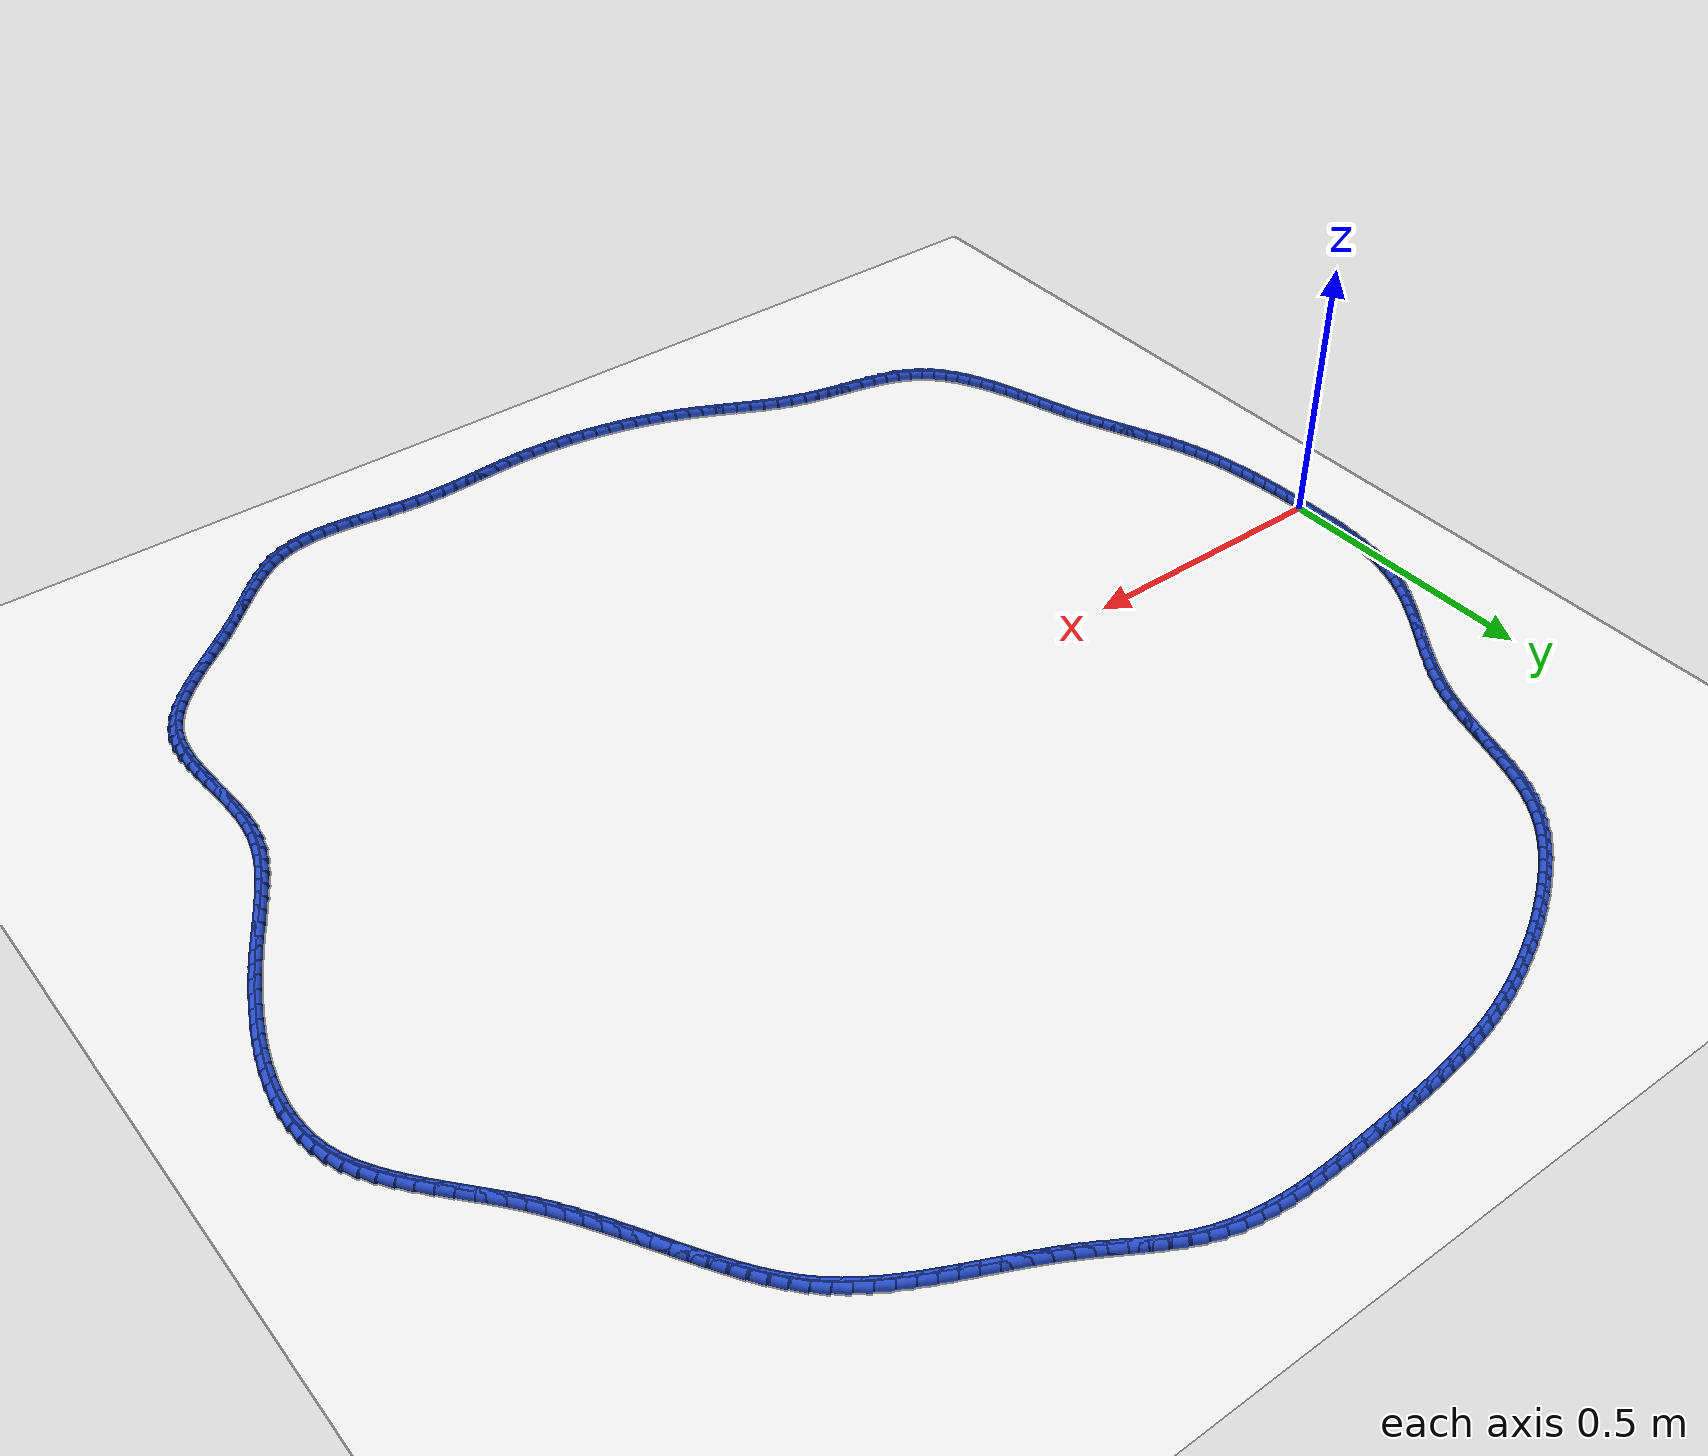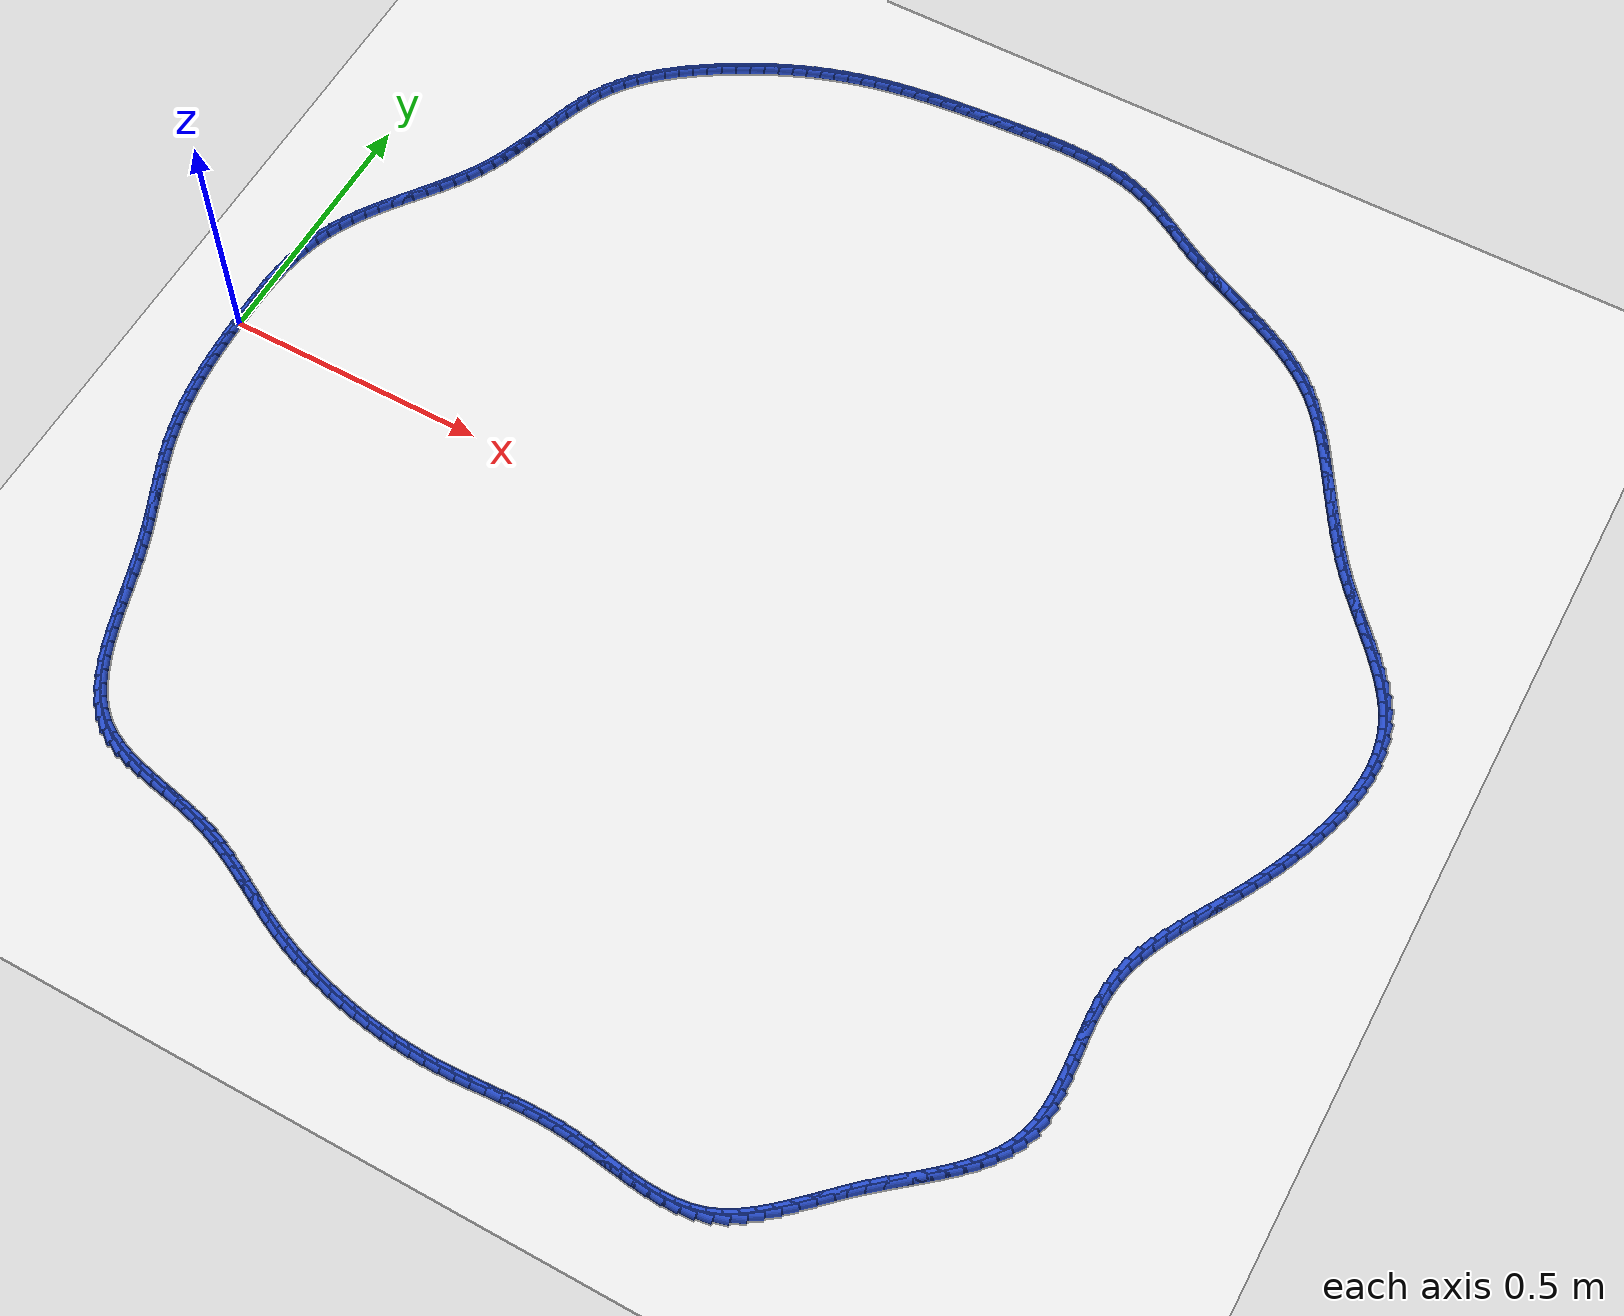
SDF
<sdf version="1.6">
 <world name="default">
  <light name="sun" type="directional">
   <pose>0 0 10 0 -0 0</pose>
   <diffuse>0.8 0.8 0.8 1</diffuse>
   <specular>0.2 0.2 0.2 1</specular>
   <attenuation>
    <range>1000</range>
    <constant>0.9</constant>
    <linear>0.01</linear>
    <quadratic>0.001</quadratic>
   </attenuation>
   <direction>-0.5 0.1 -0.9</direction>
  </light>
  <model name="ground_plane">
   <static>1</static>
   <link name="link">
    <collision name="collision">
     <geometry><plane><normal>0 0 1</normal><size>100 100</size></plane></geometry>
     <surface><friction><ode><mu>100</mu><mu2>50</mu2></ode></friction></surface>
    </collision>
    <visual name="visual">
     <cast_shadows>0</cast_shadows>
     <geometry><plane><normal>0 0 1</normal><size>100 100</size></plane></geometry>
     <material>
      <script><uri>file://media/materials/scripts/gazebo.material</uri><name>Gazebo/WhiteGlow</name></script>
     </material>
    </visual>
   </link>
  </model>
  <gravity>0 0 -9.8</gravity>
  <magnetic_field>6e-06 2.3e-05 -4.2e-05</magnetic_field>
  <atmosphere type="adiabatic"/>
  <physics name="default_physics" default="0" type="ode">
   <max_step_size>0.001</max_step_size>
   <real_time_factor>1</real_time_factor>
   <real_time_update_rate>1000</real_time_update_rate>
  </physics>
  <scene><ambient>0.4 0.4 0.4 1</ambient><background>0.7 0.7 0.7 1</background><shadows>1</shadows></scene>
  <spherical_coordinates>
   <surface_model>EARTH_WGS84</surface_model>
   <latitude_deg>0</latitude_deg>
   <longitude_deg>0</longitude_deg>
   <elevation>0</elevation>
   <heading_deg>0</heading_deg>
  </spherical_coordinates>
  <model name="line">
   <link name="link_0">
    <pose>2.168404344971009e-18 -9.020562075079397e-17 0.01 0 1.57 -1.555804678287326</pose>
    <collision name="collision">
     <geometry><cylinder><radius>0.01</radius><length>0.08</length></cylinder></geometry>
    </collision>
    <visual name="visual">
     <material>
      <script><name>Gazebo/Blue</name><uri>file://media/materials/scripts/gazebo.material</uri></script>
     </material>
     <geometry><cylinder><radius>0.01</radius><length>0.08</length></cylinder></geometry>
    </visual>
   </link>
   <link name="link_1">
    <pose>-0.00041804875525708335 0.02788335357673787 0.01 0 1.57 1.5677613581458083</pose>
    <collision name="collision">
     <geometry><cylinder><radius>0.01</radius><length>0.08</length></cylinder></geometry>
    </collision>
    <visual name="visual">
     <material>
      <script><name>Gazebo/Blue</name><uri>file://media/materials/scripts/gazebo.material</uri></script>
     </material>
     <geometry><cylinder><radius>0.01</radius><length>0.08</length></cylinder></geometry>
    </visual>
   </link>
   <link name="link_2">
    <pose>-0.0003334461583093742 0.05575920567616949 0.01 0 1.57 1.5433722922550555</pose>
    <collision name="collision">
     <geometry><cylinder><radius>0.01</radius><length>0.08</length></cylinder></geometry>
    </collision>
    <visual name="visual">
     <material>
      <script><name>Gazebo/Blue</name><uri>file://media/materials/scripts/gazebo.material</uri></script>
     </material>
     <geometry><cylinder><radius>0.01</radius><length>0.08</length></cylinder></geometry>
    </visual>
   </link>
   <link name="link_3">
    <pose>0.00042833921404787775 0.08353026130812788 0.01 0 1.57 1.5123370714789628</pose>
    <collision name="collision">
     <geometry><cylinder><radius>0.01</radius><length>0.08</length></cylinder></geometry>
    </collision>
    <visual name="visual">
     <material>
      <script><name>Gazebo/Blue</name><uri>file://media/materials/scripts/gazebo.material</uri></script>
     </material>
     <geometry><cylinder><radius>0.01</radius><length>0.08</length></cylinder></geometry>
    </visual>
   </link>
   <link name="link_4">
    <pose>0.00204183878501942 0.11109922548244619 0.01 0 1.57 1.4742951656398995</pose>
    <collision name="collision">
     <geometry><cylinder><radius>0.01</radius><length>0.08</length></cylinder></geometry>
    </collision>
    <visual name="visual">
     <material>
      <script><name>Gazebo/Blue</name><uri>file://media/materials/scripts/gazebo.material</uri></script>
     </material>
     <geometry><cylinder><radius>0.01</radius><length>0.08</length></cylinder></geometry>
    </visual>
   </link>
   <link name="link_5">
    <pose>0.004681583977809999 0.13836880320895753 0.01 0 1.57 1.4288432194086575</pose>
    <collision name="collision">
     <geometry><cylinder><radius>0.01</radius><length>0.08</length></cylinder></geometry>
    </collision>
    <visual name="visual">
     <material>
      <script><name>Gazebo/Blue</name><uri>file://media/materials/scripts/gazebo.material</uri></script>
     </material>
     <geometry><cylinder><radius>0.01</radius><length>0.08</length></cylinder></geometry>
    </visual>
   </link>
   <link name="link_6">
    <pose>0.008522106215624365 0.16524169949749504 0.01 0 1.57 1.3755870765681562</pose>
    <collision name="collision">
     <geometry><cylinder><radius>0.01</radius><length>0.08</length></cylinder></geometry>
    </collision>
    <visual name="visual">
     <material>
      <script><name>Gazebo/Blue</name><uri>file://media/materials/scripts/gazebo.material</uri></script>
     </material>
     <geometry><cylinder><radius>0.01</radius><length>0.08</length></cylinder></geometry>
    </visual>
   </link>
   <link name="link_7">
    <pose>0.013737936921667266 0.19162061935789182 0.01 0 1.57 1.3142181358839318</pose>
    <collision name="collision">
     <geometry><cylinder><radius>0.01</radius><length>0.08</length></cylinder></geometry>
    </collision>
    <visual name="visual">
     <material>
      <script><name>Gazebo/Blue</name><uri>file://media/materials/scripts/gazebo.material</uri></script>
     </material>
     <geometry><cylinder><radius>0.01</radius><length>0.08</length></cylinder></geometry>
    </visual>
   </link>
   <link name="link_8">
    <pose>0.020503607519143447 0.21740826779998096 0.01 0 1.57 1.2446174004330555</pose>
    <collision name="collision">
     <geometry><cylinder><radius>0.01</radius><length>0.08</length></cylinder></geometry>
    </collision>
    <visual name="visual">
     <material>
      <script><name>Gazebo/Blue</name><uri>file://media/materials/scripts/gazebo.material</uri></script>
     </material>
     <geometry><cylinder><radius>0.01</radius><length>0.08</length></cylinder></geometry>
    </visual>
   </link>
   <link name="link_9">
    <pose>0.028993649431257665 0.24250734983359565 0.01 0 1.57 1.1683516715750837</pose>
    <collision name="collision">
     <geometry><cylinder><radius>0.01</radius><length>0.08</length></cylinder></geometry>
    </collision>
    <visual name="visual">
     <material>
      <script><name>Gazebo/Blue</name><uri>file://media/materials/scripts/gazebo.material</uri></script>
     </material>
     <geometry><cylinder><radius>0.01</radius><length>0.08</length></cylinder></geometry>
    </visual>
   </link>
   <link name="link_10">
    <pose>0.039350084687493445 0.2668366288274649 0.01 0 1.57 1.0979912688393525</pose>
    <collision name="collision">
     <geometry><cylinder><radius>0.01</radius><length>0.08</length></cylinder></geometry>
    </collision>
    <visual name="visual">
     <material>
      <script><name>Gazebo/Blue</name><uri>file://media/materials/scripts/gazebo.material</uri></script>
     </material>
     <geometry><cylinder><radius>0.01</radius><length>0.08</length></cylinder></geometry>
    </visual>
   </link>
   <link name="link_11">
    <pose>0.05143095082864313 0.29045514529234673 0.01 0 1.57 1.0402280914805118</pose>
    <collision name="collision">
     <geometry><cylinder><radius>0.01</radius><length>0.08</length></cylinder></geometry>
    </collision>
    <visual name="visual">
     <material>
      <script><name>Gazebo/Blue</name><uri>file://media/materials/scripts/gazebo.material</uri></script>
     </material>
     <geometry><cylinder><radius>0.01</radius><length>0.08</length></cylinder></geometry>
    </visual>
   </link>
   <link name="link_12">
    <pose>0.06494762483956859 0.31349438427189996 0.01 0 1.57 0.9951122047299491</pose>
    <collision name="collision">
     <geometry><cylinder><radius>0.01</radius><length>0.08</length></cylinder></geometry>
    </collision>
    <visual name="visual">
     <material>
      <script><name>Gazebo/Blue</name><uri>file://media/materials/scripts/gazebo.material</uri></script>
     </material>
     <geometry><cylinder><radius>0.01</radius><length>0.08</length></cylinder></geometry>
    </visual>
   </link>
   <link name="link_13">
    <pose>0.07961025847958947 0.33608643602289934 0.01 0 1.57 0.9623372005283656</pose>
    <collision name="collision">
     <geometry><cylinder><radius>0.01</radius><length>0.08</length></cylinder></geometry>
    </collision>
    <visual name="visual">
     <material>
      <script><name>Gazebo/Blue</name><uri>file://media/materials/scripts/gazebo.material</uri></script>
     </material>
     <geometry><cylinder><radius>0.01</radius><length>0.08</length></cylinder></geometry>
    </visual>
   </link>
   <link name="link_14">
    <pose>0.09512900350802551 0.35836339080212004 0.01 0 1.57 0.9415063660519493</pose>
    <collision name="collision">
     <geometry><cylinder><radius>0.01</radius><length>0.08</length></cylinder></geometry>
    </collision>
    <visual name="visual">
     <material>
      <script><name>Gazebo/Blue</name><uri>file://media/materials/scripts/gazebo.material</uri></script>
     </material>
     <geometry><cylinder><radius>0.01</radius><length>0.08</length></cylinder></geometry>
    </visual>
   </link>
   <link name="link_15">
    <pose>0.11121401168419631 0.380457338866337 0.01 0 1.57 0.9322741979206398</pose>
    <collision name="collision">
     <geometry><cylinder><radius>0.01</radius><length>0.08</length></cylinder></geometry>
    </collision>
    <visual name="visual">
     <material>
      <script><name>Gazebo/Blue</name><uri>file://media/materials/scripts/gazebo.material</uri></script>
     </material>
     <geometry><cylinder><radius>0.01</radius><length>0.08</length></cylinder></geometry>
    </visual>
   </link>
   <link name="link_16">
    <pose>0.1275754347674216 0.40250037047232534 0.01 0 1.57 0.9344250344870828</pose>
    <collision name="collision">
     <geometry><cylinder><radius>0.01</radius><length>0.08</length></cylinder></geometry>
    </collision>
    <visual name="visual">
     <material>
      <script><name>Gazebo/Blue</name><uri>file://media/materials/scripts/gazebo.material</uri></script>
     </material>
     <geometry><cylinder><radius>0.01</radius><length>0.08</length></cylinder></geometry>
    </visual>
   </link>
   <link name="link_17">
    <pose>0.14392342451702111 0.4246245758768601 0.01 0 1.57 0.947902521508266</pose>
    <collision name="collision">
     <geometry><cylinder><radius>0.01</radius><length>0.08</length></cylinder></geometry>
    </collision>
    <visual name="visual">
     <material>
      <script><name>Gazebo/Blue</name><uri>file://media/materials/scripts/gazebo.material</uri></script>
     </material>
     <geometry><cylinder><radius>0.01</radius><length>0.08</length></cylinder></geometry>
    </visual>
   </link>
   <link name="link_18">
    <pose>0.15996813269231455 0.4469620453367162 0.01 0 1.57 0.972798388985565</pose>
    <collision name="collision">
     <geometry><cylinder><radius>0.01</radius><length>0.08</length></cylinder></geometry>
    </collision>
    <visual name="visual">
     <material>
      <script><name>Gazebo/Blue</name><uri>file://media/materials/scripts/gazebo.material</uri></script>
     </material>
     <geometry><cylinder><radius>0.01</radius><length>0.08</length></cylinder></geometry>
    </visual>
   </link>
   <link name="link_19">
    <pose>0.17541971105262139 0.4696448691086685 0.01 0 1.57 1.0093012895549405</pose>
    <collision name="collision">
     <geometry><cylinder><radius>0.01</radius><length>0.08</length></cylinder></geometry>
    </collision>
    <visual name="visual">
     <material>
      <script><name>Gazebo/Blue</name><uri>file://media/materials/scripts/gazebo.material</uri></script>
     </material>
     <geometry><cylinder><radius>0.01</radius><length>0.08</length></cylinder></geometry>
    </visual>
   </link>
   <link name="link_20">
    <pose>0.18998831135726163 0.4928051374494925 0.01 0 1.57 1.057599973612592</pose>
    <collision name="collision">
     <geometry><cylinder><radius>0.01</radius><length>0.08</length></cylinder></geometry>
    </collision>
    <visual name="visual">
     <material>
      <script><name>Gazebo/Blue</name><uri>file://media/materials/scripts/gazebo.material</uri></script>
     </material>
     <geometry><cylinder><radius>0.01</radius><length>0.08</length></cylinder></geometry>
    </visual>
   </link>
   <link name="link_21">
    <pose>0.20338408536555477 0.5165749406159629 0.01 0 1.57 1.1171899864930799</pose>
    <collision name="collision">
     <geometry><cylinder><radius>0.01</radius><length>0.08</length></cylinder></geometry>
    </collision>
    <visual name="visual">
     <material>
      <script><name>Gazebo/Blue</name><uri>file://media/materials/scripts/gazebo.material</uri></script>
     </material>
     <geometry><cylinder><radius>0.01</radius><length>0.08</length></cylinder></geometry>
    </visual>
   </link>
   <link name="link_22">
    <pose>0.21533039753902353 0.5410796585803513 0.01 0 1.57 1.1752956946109956</pose>
    <collision name="collision">
     <geometry><cylinder><radius>0.01</radius><length>0.08</length></cylinder></geometry>
    </collision>
    <visual name="visual">
     <material>
      <script><name>Gazebo/Blue</name><uri>file://media/materials/scripts/gazebo.material</uri></script>
     </material>
     <geometry><cylinder><radius>0.01</radius><length>0.08</length></cylinder></geometry>
    </visual>
   </link>
   <link name="link_23">
    <pose>0.22585561039555185 0.5662897731192621 0.01 0 1.57 1.2192326725221612</pose>
    <collision name="collision">
     <geometry><cylinder><radius>0.01</radius><length>0.08</length></cylinder></geometry>
    </collision>
    <visual name="visual">
     <material>
      <script><name>Gazebo/Blue</name><uri>file://media/materials/scripts/gazebo.material</uri></script>
     </material>
     <geometry><cylinder><radius>0.01</radius><length>0.08</length></cylinder></geometry>
    </visual>
   </link>
   <link name="link_24">
    <pose>0.23529370016952308 0.5920205551406733 0.01 0 1.57 1.2486441904424388</pose>
    <collision name="collision">
     <geometry><cylinder><radius>0.01</radius><length>0.08</length></cylinder></geometry>
    </collision>
    <visual name="visual">
     <material>
      <script><name>Gazebo/Blue</name><uri>file://media/materials/scripts/gazebo.material</uri></script>
     </material>
     <geometry><cylinder><radius>0.01</radius><length>0.08</length></cylinder></geometry>
    </visual>
   </link>
   <link name="link_25">
    <pose>0.2439919789297083 0.6180805027333885 0.01 0 1.57 1.2637776436564487</pose>
    <collision name="collision">
     <geometry><cylinder><radius>0.01</radius><length>0.08</length></cylinder></geometry>
    </collision>
    <visual name="visual">
     <material>
      <script><name>Gazebo/Blue</name><uri>file://media/materials/scripts/gazebo.material</uri></script>
     </material>
     <geometry><cylinder><radius>0.01</radius><length>0.08</length></cylinder></geometry>
    </visual>
   </link>
   <link name="link_26">
    <pose>0.2522977587448785 0.6442781139862113 0.01 0 1.57 1.2647552210867419</pose>
    <collision name="collision">
     <geometry><cylinder><radius>0.01</radius><length>0.08</length></cylinder></geometry>
    </collision>
    <visual name="visual">
     <material>
      <script><name>Gazebo/Blue</name><uri>file://media/materials/scripts/gazebo.material</uri></script>
     </material>
     <geometry><cylinder><radius>0.01</radius><length>0.08</length></cylinder></geometry>
    </visual>
   </link>
   <link name="link_27">
    <pose>0.2605583516838046 0.670421886987945 0.01 0 1.57 1.2514835519428156</pose>
    <collision name="collision">
     <geometry><cylinder><radius>0.01</radius><length>0.08</length></cylinder></geometry>
    </collision>
    <visual name="visual">
     <material>
      <script><name>Gazebo/Blue</name><uri>file://media/materials/scripts/gazebo.material</uri></script>
     </material>
     <geometry><cylinder><radius>0.01</radius><length>0.08</length></cylinder></geometry>
    </visual>
   </link>
   <link name="link_28">
    <pose>0.2691210698152577 0.6963203198273932 0.01 0 1.57 1.2236429030320435</pose>
    <collision name="collision">
     <geometry><cylinder><radius>0.01</radius><length>0.08</length></cylinder></geometry>
    </collision>
    <visual name="visual">
     <material>
      <script><name>Gazebo/Blue</name><uri>file://media/materials/scripts/gazebo.material</uri></script>
     </material>
     <geometry><cylinder><radius>0.01</radius><length>0.08</length></cylinder></geometry>
    </visual>
   </link>
   <link name="link_29">
    <pose>0.27833322520800885 0.7217819105933594 0.01 0 1.57 1.1807592414857768</pose>
    <collision name="collision">
     <geometry><cylinder><radius>0.01</radius><length>0.08</length></cylinder></geometry>
    </collision>
    <visual name="visual">
     <material>
      <script><name>Gazebo/Blue</name><uri>file://media/materials/scripts/gazebo.material</uri></script>
     </material>
     <geometry><cylinder><radius>0.01</radius><length>0.08</length></cylinder></geometry>
    </visual>
   </link>
   <link name="link_30">
    <pose>0.28854212993082906 0.7466151573746472 0.01 0 1.57 1.122378694512556</pose>
    <collision name="collision">
     <geometry><cylinder><radius>0.01</radius><length>0.08</length></cylinder></geometry>
    </collision>
    <visual name="visual">
     <material>
      <script><name>Gazebo/Blue</name><uri>file://media/materials/scripts/gazebo.material</uri></script>
     </material>
     <geometry><cylinder><radius>0.01</radius><length>0.08</length></cylinder></geometry>
    </visual>
   </link>
   <link name="link_31">
    <pose>0.3000950960524893 0.77062855826006 0.01 0 1.57 1.048368953539662</pose>
    <collision name="collision">
     <geometry><cylinder><radius>0.01</radius><length>0.08</length></cylinder></geometry>
    </collision>
    <visual name="visual">
     <material>
      <script><name>Gazebo/Blue</name><uri>file://media/materials/scripts/gazebo.material</uri></script>
     </material>
     <geometry><cylinder><radius>0.01</radius><length>0.08</length></cylinder></geometry>
    </visual>
   </link>
   <link name="link_32">
    <pose>0.31333943564176064 0.7936306113384014 0.01 0 1.57 0.9631495357289305</pose>
    <collision name="collision">
     <geometry><cylinder><radius>0.01</radius><length>0.08</length></cylinder></geometry>
    </collision>
    <visual name="visual">
     <material>
      <script><name>Gazebo/Blue</name><uri>file://media/materials/scripts/gazebo.material</uri></script>
     </material>
     <geometry><cylinder><radius>0.01</radius><length>0.08</length></cylinder></geometry>
    </visual>
   </link>
   <link name="link_33">
    <pose>0.32852818111363963 0.81547166322142 0.01 0 1.57 0.8829360367698877</pose>
    <collision name="collision">
     <geometry><cylinder><radius>0.01</radius><length>0.08</length></cylinder></geometry>
    </collision>
    <visual name="visual">
     <material>
      <script><name>Gazebo/Blue</name><uri>file://media/materials/scripts/gazebo.material</uri></script>
     </material>
     <geometry><cylinder><radius>0.01</radius><length>0.08</length></cylinder></geometry>
    </visual>
   </link>
   <link name="link_34">
    <pose>0.34553669353886574 0.8361696999561314 0.01 0 1.57 0.8117078359685747</pose>
    <collision name="collision">
     <geometry><cylinder><radius>0.01</radius><length>0.08</length></cylinder></geometry>
    </collision>
    <visual name="visual">
     <material>
      <script><name>Gazebo/Blue</name><uri>file://media/materials/scripts/gazebo.material</uri></script>
     </material>
     <geometry><cylinder><radius>0.01</radius><length>0.08</length></cylinder></geometry>
    </visual>
   </link>
   <link name="link_35">
    <pose>0.3641457777673561 0.8557846788741106 0.01 0 1.57 0.7491647371227234</pose>
    <collision name="collision">
     <geometry><cylinder><radius>0.01</radius><length>0.08</length></cylinder></geometry>
    </collision>
    <visual name="visual">
     <material>
      <script><name>Gazebo/Blue</name><uri>file://media/materials/scripts/gazebo.material</uri></script>
     </material>
     <geometry><cylinder><radius>0.01</radius><length>0.08</length></cylinder></geometry>
    </visual>
   </link>
   <link name="link_36">
    <pose>0.384136238649017 0.8743765573069368 0.01 0 1.57 0.6947810538954751</pose>
    <collision name="collision">
     <geometry><cylinder><radius>0.01</radius><length>0.08</length></cylinder></geometry>
    </collision>
    <visual name="visual">
     <material>
      <script><name>Gazebo/Blue</name><uri>file://media/materials/scripts/gazebo.material</uri></script>
     </material>
     <geometry><cylinder><radius>0.01</radius><length>0.08</length></cylinder></geometry>
    </visual>
   </link>
   <link name="link_37">
    <pose>0.4052888810337545 0.8920052925861893 0.01 0 1.57 0.6479418657695787</pose>
    <collision name="collision">
     <geometry><cylinder><radius>0.01</radius><length>0.08</length></cylinder></geometry>
    </collision>
    <visual name="visual">
     <material>
      <script><name>Gazebo/Blue</name><uri>file://media/materials/scripts/gazebo.material</uri></script>
     </material>
     <geometry><cylinder><radius>0.01</radius><length>0.08</length></cylinder></geometry>
    </visual>
   </link>
   <link name="link_38">
    <pose>0.42738450977147474 0.9087308420434481 0.01 0 1.57 0.6080364912030934</pose>
    <collision name="collision">
     <geometry><cylinder><radius>0.01</radius><length>0.08</length></cylinder></geometry>
    </collision>
    <visual name="visual">
     <material>
      <script><name>Gazebo/Blue</name><uri>file://media/materials/scripts/gazebo.material</uri></script>
     </material>
     <geometry><cylinder><radius>0.01</radius><length>0.08</length></cylinder></geometry>
    </visual>
   </link>
   <link name="link_39">
    <pose>0.450203929712084 0.9246131630102927 0.01 0 1.57 0.5745146182743402</pose>
    <collision name="collision">
     <geometry><cylinder><radius>0.01</radius><length>0.08</length></cylinder></geometry>
    </collision>
    <visual name="visual">
     <material>
      <script><name>Gazebo/Blue</name><uri>file://media/materials/scripts/gazebo.material</uri></script>
     </material>
     <geometry><cylinder><radius>0.01</radius><length>0.08</length></cylinder></geometry>
    </visual>
   </link>
   <link name="link_40">
    <pose>0.47352804166693796 0.9397121781923473 0.01 0 1.57 0.5454172004428118</pose>
    <collision name="collision">
     <geometry><cylinder><radius>0.01</radius><length>0.08</length></cylinder></geometry>
    </collision>
    <visual name="visual">
     <material>
      <script><name>Gazebo/Blue</name><uri>file://media/materials/scripts/gazebo.material</uri></script>
     </material>
     <geometry><cylinder><radius>0.01</radius><length>0.08</length></cylinder></geometry>
    </visual>
   </link>
   <link name="link_41">
    <pose>0.4971882328180453 0.9540695932006136 0.01 0 1.57 0.5165480859321171</pose>
    <collision name="collision">
     <geometry><cylinder><radius>0.01</radius><length>0.08</length></cylinder></geometry>
    </collision>
    <visual name="visual">
     <material>
      <script><name>Gazebo/Blue</name><uri>file://media/materials/scripts/gazebo.material</uri></script>
     </material>
     <geometry><cylinder><radius>0.01</radius><length>0.08</length></cylinder></geometry>
    </visual>
   </link>
   <link name="link_42">
    <pose>0.5211490845938066 0.9676790529089419 0.01 0 1.57 0.4872291533963207</pose>
    <collision name="collision">
     <geometry><cylinder><radius>0.01</radius><length>0.08</length></cylinder></geometry>
    </collision>
    <visual name="visual">
     <material>
      <script><name>Gazebo/Blue</name><uri>file://media/materials/scripts/gazebo.material</uri></script>
     </material>
     <geometry><cylinder><radius>0.01</radius><length>0.08</length></cylinder></geometry>
    </visual>
   </link>
   <link name="link_43">
    <pose>0.545396887482984 0.9805263688690063 0.01 0 1.57 0.4574448100621902</pose>
    <collision name="collision">
     <geometry><cylinder><radius>0.01</radius><length>0.08</length></cylinder></geometry>
    </collision>
    <visual name="visual">
     <material>
      <script><name>Gazebo/Blue</name><uri>file://media/materials/scripts/gazebo.material</uri></script>
     </material>
     <geometry><cylinder><radius>0.01</radius><length>0.08</length></cylinder></geometry>
    </visual>
   </link>
   <link name="link_44">
    <pose>0.5699179319743395 0.992597352632482 0.01 0 1.57 0.42718134618423054</pose>
    <collision name="collision">
     <geometry><cylinder><radius>0.01</radius><length>0.08</length></cylinder></geometry>
    </collision>
    <visual name="visual">
     <material>
      <script><name>Gazebo/Blue</name><uri>file://media/materials/scripts/gazebo.material</uri></script>
     </material>
     <geometry><cylinder><radius>0.01</radius><length>0.08</length></cylinder></geometry>
    </visual>
   </link>
   <link name="link_45">
    <pose>0.594698508556636 1.003877815751044 0.01 0 1.57 0.39642723890368153</pose>
    <collision name="collision">
     <geometry><cylinder><radius>0.01</radius><length>0.08</length></cylinder></geometry>
    </collision>
    <visual name="visual">
     <material>
      <script><name>Gazebo/Blue</name><uri>file://media/materials/scripts/gazebo.material</uri></script>
     </material>
     <geometry><cylinder><radius>0.01</radius><length>0.08</length></cylinder></geometry>
    </visual>
   </link>
   <link name="link_46">
    <pose>0.6197249077186352 1.0143535697763661 0.01 0 1.57 0.3651734727999431</pose>
    <collision name="collision">
     <geometry><cylinder><radius>0.01</radius><length>0.08</length></cylinder></geometry>
    </collision>
    <visual name="visual">
     <material>
      <script><name>Gazebo/Blue</name><uri>file://media/materials/scripts/gazebo.material</uri></script>
     </material>
     <geometry><cylinder><radius>0.01</radius><length>0.08</length></cylinder></geometry>
    </visual>
   </link>
   <link name="link_47">
    <pose>0.6449834199490999 1.0240104262601242 0.01 0 1.57 0.333413872990056</pose>
    <collision name="collision">
     <geometry><cylinder><radius>0.01</radius><length>0.08</length></cylinder></geometry>
    </collision>
    <visual name="visual">
     <material>
      <script><name>Gazebo/Blue</name><uri>file://media/materials/scripts/gazebo.material</uri></script>
     </material>
     <geometry><cylinder><radius>0.01</radius><length>0.08</length></cylinder></geometry>
    </visual>
   </link>
   <link name="link_48">
    <pose>0.6704603357367918 1.0328341967539922 0.01 0 1.57 0.3011454452451619</pose>
    <collision name="collision">
     <geometry><cylinder><radius>0.01</radius><length>0.08</length></cylinder></geometry>
    </collision>
    <visual name="visual">
     <material>
      <script><name>Gazebo/Blue</name><uri>file://media/materials/scripts/gazebo.material</uri></script>
     </material>
     <geometry><cylinder><radius>0.01</radius><length>0.08</length></cylinder></geometry>
    </visual>
   </link>
   <link name="link_49">
    <pose>0.6961419455704738 1.0408106928096454 0.01 0 1.57 0.26836871610626073</pose>
    <collision name="collision">
     <geometry><cylinder><radius>0.01</radius><length>0.08</length></cylinder></geometry>
    </collision>
    <visual name="visual">
     <material>
      <script><name>Gazebo/Blue</name><uri>file://media/materials/scripts/gazebo.material</uri></script>
     </material>
     <geometry><cylinder><radius>0.01</radius><length>0.08</length></cylinder></geometry>
    </visual>
   </link>
   <link name="link_50">
    <pose>0.7220145399389075 1.0479257259787578 0.01 0 1.57 0.23538729435876612</pose>
    <collision name="collision">
     <geometry><cylinder><radius>0.01</radius><length>0.08</length></cylinder></geometry>
    </collision>
    <visual name="visual">
     <material>
      <script><name>Gazebo/Blue</name><uri>file://media/materials/scripts/gazebo.material</uri></script>
     </material>
     <geometry><cylinder><radius>0.01</radius><length>0.08</length></cylinder></geometry>
    </visual>
   </link>
   <link name="link_51">
    <pose>0.7480654811254351 1.0541736075359722 0.01 0 1.57 0.20432254405779338</pose>
    <collision name="collision">
     <geometry><cylinder><radius>0.01</radius><length>0.08</length></cylinder></geometry>
    </collision>
    <visual name="visual">
     <material>
      <script><name>Gazebo/Blue</name><uri>file://media/materials/scripts/gazebo.material</uri></script>
     </material>
     <geometry><cylinder><radius>0.01</radius><length>0.08</length></cylinder></geometry>
    </visual>
   </link>
   <link name="link_52">
    <pose>0.774289566241013 1.0596076096578333 0.01 0 1.57 0.1761565881162977</pose>
    <collision name="collision">
     <geometry><cylinder><radius>0.01</radius><length>0.08</length></cylinder></geometry>
    </collision>
    <visual name="visual">
     <material>
      <script><name>Gazebo/Blue</name><uri>file://media/materials/scripts/gazebo.material</uri></script>
     </material>
     <geometry><cylinder><radius>0.01</radius><length>0.08</length></cylinder></geometry>
    </visual>
   </link>
   <link name="link_53">
    <pose>0.8006847434589618 1.0643059935977692 0.01 0 1.57 0.15096878190605903</pose>
    <collision name="collision">
     <geometry><cylinder><radius>0.01</radius><length>0.08</length></cylinder></geometry>
    </collision>
    <visual name="visual">
     <material>
      <script><name>Gazebo/Blue</name><uri>file://media/materials/scripts/gazebo.material</uri></script>
     </material>
     <geometry><cylinder><radius>0.01</radius><length>0.08</length></cylinder></geometry>
    </visual>
   </link>
   <link name="link_54">
    <pose>0.8272489723204399 1.0683471107603175 0.01 0 1.57 0.12880190662770746</pose>
    <collision name="collision">
     <geometry><cylinder><radius>0.01</radius><length>0.08</length></cylinder></geometry>
    </collision>
    <visual name="visual">
     <material>
      <script><name>Gazebo/Blue</name><uri>file://media/materials/scripts/gazebo.material</uri></script>
     </material>
     <geometry><cylinder><radius>0.01</radius><length>0.08</length></cylinder></geometry>
    </visual>
   </link>
   <link name="link_55">
    <pose>0.8539802123666046 1.071809312550013 0.01 0 1.57 0.1096717388620593</pose>
    <collision name="collision">
     <geometry><cylinder><radius>0.01</radius><length>0.08</length></cylinder></geometry>
    </collision>
    <visual name="visual">
     <material>
      <script><name>Gazebo/Blue</name><uri>file://media/materials/scripts/gazebo.material</uri></script>
     </material>
     <geometry><cylinder><radius>0.01</radius><length>0.08</length></cylinder></geometry>
    </visual>
   </link>
   <link name="link_56">
    <pose>0.8808764231386141 1.074770950371392 0.01 0 1.57 0.09357315675796929</pose>
    <collision name="collision">
     <geometry><cylinder><radius>0.01</radius><length>0.08</length></cylinder></geometry>
    </collision>
    <visual name="visual">
     <material>
      <script><name>Gazebo/Blue</name><uri>file://media/materials/scripts/gazebo.material</uri></script>
     </material>
     <geometry><cylinder><radius>0.01</radius><length>0.08</length></cylinder></geometry>
    </visual>
   </link>
   <link name="link_57">
    <pose>0.9079355641776261 1.0773103756289906 0.01 0 1.57 0.08048562304797204</pose>
    <collision name="collision">
     <geometry><cylinder><radius>0.01</radius><length>0.08</length></cylinder></geometry>
    </collision>
    <visual name="visual">
     <material>
      <script><name>Gazebo/Blue</name><uri>file://media/materials/scripts/gazebo.material</uri></script>
     </material>
     <geometry><cylinder><radius>0.01</radius><length>0.08</length></cylinder></geometry>
    </visual>
   </link>
   <link name="link_58">
    <pose>0.935155595024799 1.079505939727345 0.01 0 1.57 0.07037785075396566</pose>
    <collision name="collision">
     <geometry><cylinder><radius>0.01</radius><length>0.08</length></cylinder></geometry>
    </collision>
    <visual name="visual">
     <material>
      <script><name>Gazebo/Blue</name><uri>file://media/materials/scripts/gazebo.material</uri></script>
     </material>
     <geometry><cylinder><radius>0.01</radius><length>0.08</length></cylinder></geometry>
    </visual>
   </link>
   <link name="link_59">
    <pose>0.9625344752212897 1.0814359940709903 0.01 0 1.57 0.06321156536309994</pose>
    <collision name="collision">
     <geometry><cylinder><radius>0.01</radius><length>0.08</length></cylinder></geometry>
    </collision>
    <visual name="visual">
     <material>
      <script><name>Gazebo/Blue</name><uri>file://media/materials/scripts/gazebo.material</uri></script>
     </material>
     <geometry><cylinder><radius>0.01</radius><length>0.08</length></cylinder></geometry>
    </visual>
   </link>
   <link name="link_60">
    <pose>0.9900701643082565 1.083178890064463 0.01 0 1.57 0.05894206870078785</pose>
    <collision name="collision">
     <geometry><cylinder><radius>0.01</radius><length>0.08</length></cylinder></geometry>
    </collision>
    <visual name="visual">
     <material>
      <script><name>Gazebo/Blue</name><uri>file://media/materials/scripts/gazebo.material</uri></script>
     </material>
     <geometry><cylinder><radius>0.01</radius><length>0.08</length></cylinder></geometry>
    </visual>
   </link>
   <link name="link_61">
    <pose>1.0177606023802859 1.0848129144975867 0.01 0 1.57 0.05534965766220769</pose>
    <collision name="collision">
     <geometry><cylinder><radius>0.01</radius><length>0.08</length></cylinder></geometry>
    </collision>
    <visual name="visual">
     <material>
      <script><name>Gazebo/Blue</name><uri>file://media/materials/scripts/gazebo.material</uri></script>
     </material>
     <geometry><cylinder><radius>0.01</radius><length>0.08</length></cylinder></geometry>
    </visual>
   </link>
   <link name="link_62">
    <pose>1.0455851340824247 1.0863545674516288 0.01 0 1.57 0.046190292588928455</pose>
    <collision name="collision">
     <geometry><cylinder><radius>0.01</radius><length>0.08</length></cylinder></geometry>
    </collision>
    <visual name="visual">
     <material>
      <script><name>Gazebo/Blue</name><uri>file://media/materials/scripts/gazebo.material</uri></script>
     </material>
     <geometry><cylinder><radius>0.01</radius><length>0.08</length></cylinder></geometry>
    </visual>
   </link>
   <link name="link_63">
    <pose>1.0734698758081547 1.0876434886174144 0.01 0 1.57 0.03029713956302984</pose>
    <collision name="collision">
     <geometry><cylinder><radius>0.01</radius><length>0.08</length></cylinder></geometry>
    </collision>
    <visual name="visual">
     <material>
      <script><name>Gazebo/Blue</name><uri>file://media/materials/scripts/gazebo.material</uri></script>
     </material>
     <geometry><cylinder><radius>0.01</radius><length>0.08</length></cylinder></geometry>
    </visual>
   </link>
   <link name="link_64">
    <pose>1.1013314805731682 1.0884878739196886 0.01 0 1.57 0.007495606614740009</pose>
    <collision name="collision">
     <geometry><cylinder><radius>0.01</radius><length>0.08</length></cylinder></geometry>
    </collision>
    <visual name="visual">
     <material>
      <script><name>Gazebo/Blue</name><uri>file://media/materials/scripts/gazebo.material</uri></script>
     </material>
     <geometry><cylinder><radius>0.01</radius><length>0.08</length></cylinder></geometry>
    </visual>
   </link>
   <link name="link_65">
    <pose>1.1290866013931578 1.0886959192831962 0.01 0 1.57 -0.022491839690040465</pose>
    <collision name="collision">
     <geometry><cylinder><radius>0.01</radius><length>0.08</length></cylinder></geometry>
    </collision>
    <visual name="visual">
     <material>
      <script><name>Gazebo/Blue</name><uri>file://media/materials/scripts/gazebo.material</uri></script>
     </material>
     <geometry><cylinder><radius>0.01</radius><length>0.08</length></cylinder></geometry>
    </visual>
   </link>
   <link name="link_66">
    <pose>1.1566518912838146 1.0880758206326813 0.01 0 1.57 -0.06002015854585055</pose>
    <collision name="collision">
     <geometry><cylinder><radius>0.01</radius><length>0.08</length></cylinder></geometry>
    </collision>
    <visual name="visual">
     <material>
      <script><name>Gazebo/Blue</name><uri>file://media/materials/scripts/gazebo.material</uri></script>
     </material>
     <geometry><cylinder><radius>0.01</radius><length>0.08</length></cylinder></geometry>
    </visual>
   </link>
   <link name="link_67">
    <pose>1.1839440032608324 1.0864357738928905 0.01 0 1.57 -0.10548180294846678</pose>
    <collision name="collision">
     <geometry><cylinder><radius>0.01</radius><length>0.08</length></cylinder></geometry>
    </collision>
    <visual name="visual">
     <material>
      <script><name>Gazebo/Blue</name><uri>file://media/materials/scripts/gazebo.material</uri></script>
     </material>
     <geometry><cylinder><radius>0.01</radius><length>0.08</length></cylinder></geometry>
    </visual>
   </link>
   <link name="link_68">
    <pose>1.2108795903399012 1.0835839749885672 0.01 0 1.57 -0.15924550258703657</pose>
    <collision name="collision">
     <geometry><cylinder><radius>0.01</radius><length>0.08</length></cylinder></geometry>
    </collision>
    <visual name="visual">
     <material>
      <script><name>Gazebo/Blue</name><uri>file://media/materials/scripts/gazebo.material</uri></script>
     </material>
     <geometry><cylinder><radius>0.01</radius><length>0.08</length></cylinder></geometry>
    </visual>
   </link>
   <link name="link_69">
    <pose>1.2373753055367145 1.0793286198444574 0.01 0 1.57 -0.22156743102996398</pose>
    <collision name="collision">
     <geometry><cylinder><radius>0.01</radius><length>0.08</length></cylinder></geometry>
    </collision>
    <visual name="visual">
     <material>
      <script><name>Gazebo/Blue</name><uri>file://media/materials/scripts/gazebo.material</uri></script>
     </material>
     <geometry><cylinder><radius>0.01</radius><length>0.08</length></cylinder></geometry>
    </visual>
   </link>
   <link name="link_70">
    <pose>1.2633478018669642 1.073477904385306 0.01 0 1.57 -0.29247282647016587</pose>
    <collision name="collision">
     <geometry><cylinder><radius>0.01</radius><length>0.08</length></cylinder></geometry>
    </collision>
    <visual name="visual">
     <material>
      <script><name>Gazebo/Blue</name><uri>file://media/materials/scripts/gazebo.material</uri></script>
     </material>
     <geometry><cylinder><radius>0.01</radius><length>0.08</length></cylinder></geometry>
    </visual>
   </link>
   <link name="link_71">
    <pose>1.2887137323463418 1.0658400245358575 0.01 0 1.57 -0.3708620241444762</pose>
    <collision name="collision">
     <geometry><cylinder><radius>0.01</radius><length>0.08</length></cylinder></geometry>
    </collision>
    <visual name="visual">
     <material>
      <script><name>Gazebo/Blue</name><uri>file://media/materials/scripts/gazebo.material</uri></script>
     </material>
     <geometry><cylinder><radius>0.01</radius><length>0.08</length></cylinder></geometry>
    </visual>
   </link>
   <link name="link_72">
    <pose>1.3133977589576755 1.0562415124613482 0.01 0 1.57 -0.4426096154959034</pose>
    <collision name="collision">
     <geometry><cylinder><radius>0.01</radius><length>0.08</length></cylinder></geometry>
    </collision>
    <visual name="visual">
     <material>
      <script><name>Gazebo/Blue</name><uri>file://media/materials/scripts/gazebo.material</uri></script>
     </material>
     <geometry><cylinder><radius>0.01</radius><length>0.08</length></cylinder></geometry>
    </visual>
   </link>
   <link name="link_73">
    <pose>1.337466387126384 1.044833645756902 0.01 0 1.57 -0.4958217156277015</pose>
    <collision name="collision">
     <geometry><cylinder><radius>0.01</radius><length>0.08</length></cylinder></geometry>
    </collision>
    <visual name="visual">
     <material>
      <script><name>Gazebo/Blue</name><uri>file://media/materials/scripts/gazebo.material</uri></script>
     </material>
     <geometry><cylinder><radius>0.01</radius><length>0.08</length></cylinder></geometry>
    </visual>
   </link>
   <link name="link_74">
    <pose>1.3611077908723621 1.0320462578626977 0.01 0 1.57 -0.5304418981407579</pose>
    <collision name="collision">
     <geometry><cylinder><radius>0.01</radius><length>0.08</length></cylinder></geometry>
    </collision>
    <visual name="visual">
     <material>
      <script><name>Gazebo/Blue</name><uri>file://media/materials/scripts/gazebo.material</uri></script>
     </material>
     <geometry><cylinder><radius>0.01</radius><length>0.08</length></cylinder></geometry>
    </visual>
   </link>
   <link name="link_75">
    <pose>1.384514088416258 1.01831821232384 0.01 0 1.57 -0.5470603381698533</pose>
    <collision name="collision">
     <geometry><cylinder><radius>0.01</radius><length>0.08</length></cylinder></geometry>
    </collision>
    <visual name="visual">
     <material>
      <script><name>Gazebo/Blue</name><uri>file://media/materials/scripts/gazebo.material</uri></script>
     </material>
     <geometry><cylinder><radius>0.01</radius><length>0.08</length></cylinder></geometry>
    </visual>
   </link>
   <link name="link_76">
    <pose>1.4078773979787194 1.0040883726854326 0.01 0 1.57 -0.5461943588893264</pose>
    <collision name="collision">
     <geometry><cylinder><radius>0.01</radius><length>0.08</length></cylinder></geometry>
    </collision>
    <visual name="visual">
     <material>
      <script><name>Gazebo/Blue</name><uri>file://media/materials/scripts/gazebo.material</uri></script>
     </material>
     <geometry><cylinder><radius>0.01</radius><length>0.08</length></cylinder></geometry>
    </visual>
   </link>
   <link name="link_77">
    <pose>1.4313898377803946 0.9897956024925799 0.01 0 1.57 -0.5281428817236964</pose>
    <collision name="collision">
     <geometry><cylinder><radius>0.01</radius><length>0.08</length></cylinder></geometry>
    </collision>
    <visual name="visual">
     <material>
      <script><name>Gazebo/Blue</name><uri>file://media/materials/scripts/gazebo.material</uri></script>
     </material>
     <geometry><cylinder><radius>0.01</radius><length>0.08</length></cylinder></geometry>
    </visual>
   </link>
   <link name="link_78">
    <pose>1.4552435251286906 0.9758787636007402 0.01 0 1.57 -0.4976418148152452</pose>
    <collision name="collision">
     <geometry><cylinder><radius>0.01</radius><length>0.08</length></cylinder></geometry>
    </collision>
    <visual name="visual">
     <material>
      <script><name>Gazebo/Blue</name><uri>file://media/materials/scripts/gazebo.material</uri></script>
     </material>
     <geometry><cylinder><radius>0.01</radius><length>0.08</length></cylinder></geometry>
    </visual>
   </link>
   <link name="link_79">
    <pose>1.4795695409290266 0.9626637906066232 0.01 0 1.57 -0.4718519954417214</pose>
    <collision name="collision">
     <geometry><cylinder><radius>0.01</radius><length>0.08</length></cylinder></geometry>
    </collision>
    <visual name="visual">
     <material>
      <script><name>Gazebo/Blue</name><uri>file://media/materials/scripts/gazebo.material</uri></script>
     </material>
     <geometry><cylinder><radius>0.01</radius><length>0.08</length></cylinder></geometry>
    </visual>
   </link>
   <link name="link_80">
    <pose>1.5042726279284846 0.9500578557464605 0.01 0 1.57 -0.45464074794217574</pose>
    <collision name="collision">
     <geometry><cylinder><radius>0.01</radius><length>0.08</length></cylinder></geometry>
    </collision>
    <visual name="visual">
     <material>
      <script><name>Gazebo/Blue</name><uri>file://media/materials/scripts/gazebo.material</uri></script>
     </material>
     <geometry><cylinder><radius>0.01</radius><length>0.08</length></cylinder></geometry>
    </visual>
   </link>
   <link name="link_81">
    <pose>1.529205075880962 0.9378710846983515 0.01 0 1.57 -0.44591737863398884</pose>
    <collision name="collision">
     <geometry><cylinder><radius>0.01</radius><length>0.08</length></cylinder></geometry>
    </collision>
    <visual name="visual">
     <material>
      <script><name>Gazebo/Blue</name><uri>file://media/materials/scripts/gazebo.material</uri></script>
     </material>
     <geometry><cylinder><radius>0.01</radius><length>0.08</length></cylinder></geometry>
    </visual>
   </link>
   <link name="link_82">
    <pose>1.5542191745403566 0.925913603140396 0.01 0 1.57 -0.4456616537423919</pose>
    <collision name="collision">
     <geometry><cylinder><radius>0.01</radius><length>0.08</length></cylinder></geometry>
    </collision>
    <visual name="visual">
     <material>
      <script><name>Gazebo/Blue</name><uri>file://media/materials/scripts/gazebo.material</uri></script>
     </material>
     <geometry><cylinder><radius>0.01</radius><length>0.08</length></cylinder></geometry>
    </visual>
   </link>
   <link name="link_83">
    <pose>1.5791672136605635 0.913995536750693 0.01 0 1.57 -0.4539428967793592</pose>
    <collision name="collision">
     <geometry><cylinder><radius>0.01</radius><length>0.08</length></cylinder></geometry>
    </collision>
    <visual name="visual">
     <material>
      <script><name>Gazebo/Blue</name><uri>file://media/materials/scripts/gazebo.material</uri></script>
     </material>
     <geometry><cylinder><radius>0.01</radius><length>0.08</length></cylinder></geometry>
    </visual>
   </link>
   <link name="link_84">
    <pose>1.6039014829954814 0.9019270112073428 0.01 0 1.57 -0.4709229744746927</pose>
    <collision name="collision">
     <geometry><cylinder><radius>0.01</radius><length>0.08</length></cylinder></geometry>
    </collision>
    <visual name="visual">
     <material>
      <script><name>Gazebo/Blue</name><uri>file://media/materials/scripts/gazebo.material</uri></script>
     </material>
     <geometry><cylinder><radius>0.01</radius><length>0.08</length></cylinder></geometry>
    </visual>
   </link>
   <link name="link_85">
    <pose>1.628274272299006 0.8895181521884443 0.01 0 1.57 -0.49684224573863983</pose>
    <collision name="collision">
     <geometry><cylinder><radius>0.01</radius><length>0.08</length></cylinder></geometry>
    </collision>
    <visual name="visual">
     <material>
      <script><name>Gazebo/Blue</name><uri>file://media/materials/scripts/gazebo.material</uri></script>
     </material>
     <geometry><cylinder><radius>0.01</radius><length>0.08</length></cylinder></geometry>
    </visual>
   </link>
   <link name="link_86">
    <pose>1.6521378713250359 0.8765790853720978 0.01 0 1.57 -0.5319849324068594</pose>
    <collision name="collision">
     <geometry><cylinder><radius>0.01</radius><length>0.08</length></cylinder></geometry>
    </collision>
    <visual name="visual">
     <material>
      <script><name>Gazebo/Blue</name><uri>file://media/materials/scripts/gazebo.material</uri></script>
     </material>
     <geometry><cylinder><radius>0.01</radius><length>0.08</length></cylinder></geometry>
    </visual>
   </link>
   <link name="link_87">
    <pose>1.6753445698274658 0.8629199364364021 0.01 0 1.57 -0.5766183289309372</pose>
    <collision name="collision">
     <geometry><cylinder><radius>0.01</radius><length>0.08</length></cylinder></geometry>
    </collision>
    <visual name="visual">
     <material>
      <script><name>Gazebo/Blue</name><uri>file://media/materials/scripts/gazebo.material</uri></script>
     </material>
     <geometry><cylinder><radius>0.01</radius><length>0.08</length></cylinder></geometry>
    </visual>
   </link>
   <link name="link_88">
    <pose>1.6977466575601943 0.8483508310594573 0.01 0 1.57 -0.6309002580454792</pose>
    <collision name="collision">
     <geometry><cylinder><radius>0.01</radius><length>0.08</length></cylinder></geometry>
    </collision>
    <visual name="visual">
     <material>
      <script><name>Gazebo/Blue</name><uri>file://media/materials/scripts/gazebo.material</uri></script>
     </material>
     <geometry><cylinder><radius>0.01</radius><length>0.08</length></cylinder></geometry>
    </visual>
   </link>
   <link name="link_89">
    <pose>1.7191964242771187 0.8326818949193627 0.01 0 1.57 -0.6947535985949771</pose>
    <collision name="collision">
     <geometry><cylinder><radius>0.01</radius><length>0.08</length></cylinder></geometry>
    </collision>
    <visual name="visual">
     <material>
      <script><name>Gazebo/Blue</name><uri>file://media/materials/scripts/gazebo.material</uri></script>
     </material>
     <geometry><cylinder><radius>0.01</radius><length>0.08</length></cylinder></geometry>
    </visual>
   </link>
   <link name="link_90">
    <pose>1.7395461597321356 0.815723253694218 0.01 0 1.57 -0.7677125456993331</pose>
    <collision name="collision">
     <geometry><cylinder><radius>0.01</radius><length>0.08</length></cylinder></geometry>
    </collision>
    <visual name="visual">
     <material>
      <script><name>Gazebo/Blue</name><uri>file://media/materials/scripts/gazebo.material</uri></script>
     </material>
     <geometry><cylinder><radius>0.01</radius><length>0.08</length></cylinder></geometry>
    </visual>
   </link>
   <link name="link_91">
    <pose>1.7586482420604739 0.7972851617654321 0.01 0 1.57 -0.8437632944353479</pose>
    <collision name="collision">
     <geometry><cylinder><radius>0.01</radius><length>0.08</length></cylinder></geometry>
    </collision>
    <visual name="visual">
     <material>
      <script><name>Gazebo/Blue</name><uri>file://media/materials/scripts/gazebo.material</uri></script>
     </material>
     <geometry><cylinder><radius>0.01</radius><length>0.08</length></cylinder></geometry>
    </visual>
   </link>
   <link name="link_92">
    <pose>1.7764336422517568 0.777292322574255 0.01 0 1.57 -0.9080763218410239</pose>
    <collision name="collision">
     <geometry><cylinder><radius>0.01</radius><length>0.08</length></cylinder></geometry>
    </collision>
    <visual name="visual">
     <material>
      <script><name>Gazebo/Blue</name><uri>file://media/materials/scripts/gazebo.material</uri></script>
     </material>
     <geometry><cylinder><radius>0.01</radius><length>0.08</length></cylinder></geometry>
    </visual>
   </link>
   <link name="link_93">
    <pose>1.7930562972148232 0.7559941286195899 0.01 0 1.57 -0.9587100588749417</pose>
    <collision name="collision">
     <geometry><cylinder><radius>0.01</radius><length>0.08</length></cylinder></geometry>
    </collision>
    <visual name="visual">
     <material>
      <script><name>Gazebo/Blue</name><uri>file://media/materials/scripts/gazebo.material</uri></script>
     </material>
     <geometry><cylinder><radius>0.01</radius><length>0.08</length></cylinder></geometry>
    </visual>
   </link>
   <link name="link_94">
    <pose>1.808709412990205 0.733697157181806 0.01 0 1.57 -0.9964474598802279</pose>
    <collision name="collision">
     <geometry><cylinder><radius>0.01</radius><length>0.08</length></cylinder></geometry>
    </collision>
    <visual name="visual">
     <material>
      <script><name>Gazebo/Blue</name><uri>file://media/materials/scripts/gazebo.material</uri></script>
     </material>
     <geometry><cylinder><radius>0.01</radius><length>0.08</length></cylinder></geometry>
    </visual>
   </link>
   <link name="link_95">
    <pose>1.8235861956184365 0.7107079855412716 0.01 0 1.57 -1.0219648035505666</pose>
    <collision name="collision">
     <geometry><cylinder><radius>0.01</radius><length>0.08</length></cylinder></geometry>
    </collision>
    <visual name="visual">
     <material>
      <script><name>Gazebo/Blue</name><uri>file://media/materials/scripts/gazebo.material</uri></script>
     </material>
     <geometry><cylinder><radius>0.01</radius><length>0.08</length></cylinder></geometry>
    </visual>
   </link>
   <link name="link_96">
    <pose>1.8378798511400485 0.6873331909783552 0.01 0 1.57 -1.0360712798955023</pose>
    <collision name="collision">
     <geometry><cylinder><radius>0.01</radius><length>0.08</length></cylinder></geometry>
    </collision>
    <visual name="visual">
     <material>
      <script><name>Gazebo/Blue</name><uri>file://media/materials/scripts/gazebo.material</uri></script>
     </material>
     <geometry><cylinder><radius>0.01</radius><length>0.08</length></cylinder></geometry>
    </visual>
   </link>
   <link name="link_97">
    <pose>1.8517807704669418 0.6638630816277493 0.01 0 1.57 -1.04271239100812</pose>
    <collision name="collision">
     <geometry><cylinder><radius>0.01</radius><length>0.08</length></cylinder></geometry>
    </collision>
    <visual name="visual">
     <material>
      <script><name>Gazebo/Blue</name><uri>file://media/materials/scripts/gazebo.material</uri></script>
     </material>
     <geometry><cylinder><radius>0.01</radius><length>0.08</length></cylinder></geometry>
    </visual>
   </link>
   <link name="link_98">
    <pose>1.865451634658521 0.6404278252946978 0.01 0 1.57 -1.0439897596024617</pose>
    <collision name="collision">
     <geometry><cylinder><radius>0.01</radius><length>0.08</length></cylinder></geometry>
    </collision>
    <visual name="visual">
     <material>
      <script><name>Gazebo/Blue</name><uri>file://media/materials/scripts/gazebo.material</uri></script>
     </material>
     <geometry><cylinder><radius>0.01</radius><length>0.08</length></cylinder></geometry>
    </visual>
   </link>
   <link name="link_99">
    <pose>1.879039372804766 0.6170665562585831 0.01 0 1.57 -1.0398599641447368</pose>
    <collision name="collision">
     <geometry><cylinder><radius>0.01</radius><length>0.08</length></cylinder></geometry>
    </collision>
    <visual name="visual">
     <material>
      <script><name>Gazebo/Blue</name><uri>file://media/materials/scripts/gazebo.material</uri></script>
     </material>
     <geometry><cylinder><radius>0.01</radius><length>0.08</length></cylinder></geometry>
    </visual>
   </link>
   <link name="link_100">
    <pose>1.8926907323231492 0.5938173588799935 0.01 0 1.57 -1.0303035044603241</pose>
    <collision name="collision">
     <geometry><cylinder><radius>0.01</radius><length>0.08</length></cylinder></geometry>
    </collision>
    <visual name="visual">
     <material>
      <script><name>Gazebo/Blue</name><uri>file://media/materials/scripts/gazebo.material</uri></script>
     </material>
     <geometry><cylinder><radius>0.01</radius><length>0.08</length></cylinder></geometry>
    </visual>
   </link>
   <link name="link_101">
    <pose>1.9065524606311453 0.5707183175195182 0.01 0 1.57 -1.0153546658575747</pose>
    <collision name="collision">
     <geometry><cylinder><radius>0.01</radius><length>0.08</length></cylinder></geometry>
    </collision>
    <visual name="visual">
     <material>
      <script><name>Gazebo/Blue</name><uri>file://media/materials/scripts/gazebo.material</uri></script>
     </material>
     <geometry><cylinder><radius>0.01</radius><length>0.08</length></cylinder></geometry>
    </visual>
   </link>
   <link name="link_102">
    <pose>1.9207713051462265 0.5478075165377456 0.01 0 1.57 -0.9951094317340377</pose>
    <collision name="collision">
     <geometry><cylinder><radius>0.01</radius><length>0.08</length></cylinder></geometry>
    </collision>
    <visual name="visual">
     <material>
      <script><name>Gazebo/Blue</name><uri>file://media/materials/scripts/gazebo.material</uri></script>
     </material>
     <geometry><cylinder><radius>0.01</radius><length>0.08</length></cylinder></geometry>
    </visual>
   </link>
   <link name="link_103">
    <pose>1.9354940132858662 0.5251230402952641 0.01 0 1.57 -0.9697359558217709</pose>
    <collision name="collision">
     <geometry><cylinder><radius>0.01</radius><length>0.08</length></cylinder></geometry>
    </collision>
    <visual name="visual">
     <material>
      <script><name>Gazebo/Blue</name><uri>file://media/materials/scripts/gazebo.material</uri></script>
     </material>
     <geometry><cylinder><radius>0.01</radius><length>0.08</length></cylinder></geometry>
    </visual>
   </link>
   <link name="link_104">
    <pose>1.950867332467538 0.5027029731526625 0.01 0 1.57 -0.9394860442144648</pose>
    <collision name="collision">
     <geometry><cylinder><radius>0.01</radius><length>0.08</length></cylinder></geometry>
    </collision>
    <visual name="visual">
     <material>
      <script><name>Gazebo/Blue</name><uri>file://media/materials/scripts/gazebo.material</uri></script>
     </material>
     <geometry><cylinder><radius>0.01</radius><length>0.08</length></cylinder></geometry>
    </visual>
   </link>
   <link name="link_105">
    <pose>1.967038010108716 0.48058539947053 0.01 0 1.57 -0.905326042271216</pose>
    <collision name="collision">
     <geometry><cylinder><radius>0.01</radius><length>0.08</length></cylinder></geometry>
    </collision>
    <visual name="visual">
     <material>
      <script><name>Gazebo/Blue</name><uri>file://media/materials/scripts/gazebo.material</uri></script>
     </material>
     <geometry><cylinder><radius>0.01</radius><length>0.08</length></cylinder></geometry>
    </visual>
   </link>
   <link name="link_106">
    <pose>1.984135054569822 0.45880316168662605 0.01 0 1.57 -0.8769935058342964</pose>
    <collision name="collision">
     <geometry><cylinder><radius>0.01</radius><length>0.08</length></cylinder></geometry>
    </collision>
    <visual name="visual">
     <material>
      <script><name>Gazebo/Blue</name><uri>file://media/materials/scripts/gazebo.material</uri></script>
     </material>
     <geometry><cylinder><radius>0.01</radius><length>0.08</length></cylinder></geometry>
    </visual>
   </link>
   <link name="link_107">
    <pose>2.0020135208179353 0.4373081485249735 0.01 0 1.57 -0.861474964989389</pose>
    <collision name="collision">
     <geometry><cylinder><radius>0.01</radius><length>0.08</length></cylinder></geometry>
    </collision>
    <visual name="visual">
     <material>
      <script><name>Gazebo/Blue</name><uri>file://media/materials/scripts/gazebo.material</uri></script>
     </material>
     <geometry><cylinder><radius>0.01</radius><length>0.08</length></cylinder></geometry>
    </visual>
   </link>
   <link name="link_108">
    <pose>2.0203131272545787 0.4159886163724565 0.01 0 1.57 -0.8585490865770606</pose>
    <collision name="collision">
     <geometry><cylinder><radius>0.01</radius><length>0.08</length></cylinder></geometry>
    </collision>
    <visual name="visual">
     <material>
      <script><name>Gazebo/Blue</name><uri>file://media/materials/scripts/gazebo.material</uri></script>
     </material>
     <geometry><cylinder><radius>0.01</radius><length>0.08</length></cylinder></geometry>
    </visual>
   </link>
   <link name="link_109">
    <pose>2.038667790017676 0.3947311070367722 0.01 0 1.57 -0.8681842586876788</pose>
    <collision name="collision">
     <geometry><cylinder><radius>0.01</radius><length>0.08</length></cylinder></geometry>
    </collision>
    <visual name="visual">
     <material>
      <script><name>Gazebo/Blue</name><uri>file://media/materials/scripts/gazebo.material</uri></script>
     </material>
     <geometry><cylinder><radius>0.01</radius><length>0.08</length></cylinder></geometry>
    </visual>
   </link>
   <link name="link_110">
    <pose>2.056711425245149 0.37342216232561737 0.01 0 1.57 -0.8907552135814855</pose>
    <collision name="collision">
     <geometry><cylinder><radius>0.01</radius><length>0.08</length></cylinder></geometry>
    </collision>
    <visual name="visual">
     <material>
      <script><name>Gazebo/Blue</name><uri>file://media/materials/scripts/gazebo.material</uri></script>
     </material>
     <geometry><cylinder><radius>0.01</radius><length>0.08</length></cylinder></geometry>
    </visual>
   </link>
   <link name="link_111">
    <pose>2.0740779490749195 0.35194832404668913 0.01 0 1.57 -0.9270249981093669</pose>
    <collision name="collision">
     <geometry><cylinder><radius>0.01</radius><length>0.08</length></cylinder></geometry>
    </collision>
    <visual name="visual">
     <material>
      <script><name>Gazebo/Blue</name><uri>file://media/materials/scripts/gazebo.material</uri></script>
     </material>
     <geometry><cylinder><radius>0.01</radius><length>0.08</length></cylinder></geometry>
    </visual>
   </link>
   <link name="link_112">
    <pose>2.0904012776449106 0.3301961340076843 0.01 0 1.57 -0.9780758287364772</pose>
    <collision name="collision">
     <geometry><cylinder><radius>0.01</radius><length>0.08</length></cylinder></geometry>
    </collision>
    <visual name="visual">
     <material>
      <script><name>Gazebo/Blue</name><uri>file://media/materials/scripts/gazebo.material</uri></script>
     </material>
     <geometry><cylinder><radius>0.01</radius><length>0.08</length></cylinder></geometry>
    </visual>
   </link>
   <link name="link_113">
    <pose>2.105315327093046 0.3080521340163001 0.01 0 1.57 -1.0451427953588288</pose>
    <collision name="collision">
     <geometry><cylinder><radius>0.01</radius><length>0.08</length></cylinder></geometry>
    </collision>
    <visual name="visual">
     <material>
      <script><name>Gazebo/Blue</name><uri>file://media/materials/scripts/gazebo.material</uri></script>
     </material>
     <geometry><cylinder><radius>0.01</radius><length>0.08</length></cylinder></geometry>
    </visual>
   </link>
   <link name="link_114">
    <pose>2.1184540135572476 0.28540286588023345 0.01 0 1.57 -1.1292804029817711</pose>
    <collision name="collision">
     <geometry><cylinder><radius>0.01</radius><length>0.08</length></cylinder></geometry>
    </collision>
    <visual name="visual">
     <material>
      <script><name>Gazebo/Blue</name><uri>file://media/materials/scripts/gazebo.material</uri></script>
     </material>
     <geometry><cylinder><radius>0.01</radius><length>0.08</length></cylinder></geometry>
    </visual>
   </link>
   <link name="link_115">
    <pose>2.1294512531754384 0.26213487140718117 0.01 0 1.57 -1.2301131521014206</pose>
    <collision name="collision">
     <geometry><cylinder><radius>0.01</radius><length>0.08</length></cylinder></geometry>
    </collision>
    <visual name="visual">
     <material>
      <script><name>Gazebo/Blue</name><uri>file://media/materials/scripts/gazebo.material</uri></script>
     </material>
     <geometry><cylinder><radius>0.01</radius><length>0.08</length></cylinder></geometry>
    </visual>
   </link>
   <link name="link_116">
    <pose>2.137957220833913 0.23814099181949167 0.01 0 1.57 -1.3351066473388362</pose>
    <collision name="collision">
     <geometry><cylinder><radius>0.01</radius><length>0.08</length></cylinder></geometry>
    </collision>
    <visual name="visual">
     <material>
      <script><name>Gazebo/Blue</name><uri>file://media/materials/scripts/gazebo.material</uri></script>
     </material>
     <geometry><cylinder><radius>0.01</radius><length>0.08</length></cylinder></geometry>
    </visual>
   </link>
   <link name="link_117">
    <pose>2.143894166270544 0.213419483114809 0.01 0 1.57 -1.433073792004144</pose>
    <collision name="collision">
     <geometry><cylinder><radius>0.01</radius><length>0.08</length></cylinder></geometry>
    </collision>
    <visual name="visual">
     <material>
      <script><name>Gazebo/Blue</name><uri>file://media/materials/scripts/gazebo.material</uri></script>
     </material>
     <geometry><cylinder><radius>0.01</radius><length>0.08</length></cylinder></geometry>
    </visual>
   </link>
   <link name="link_118">
    <pose>2.147409562495682 0.18805586352954037 0.01 0 1.57 -1.5226768742899677</pose>
    <collision name="collision">
     <geometry><cylinder><radius>0.01</radius><length>0.08</length></cylinder></geometry>
    </collision>
    <visual name="visual">
     <material>
      <script><name>Gazebo/Blue</name><uri>file://media/materials/scripts/gazebo.material</uri></script>
     </material>
     <geometry><cylinder><radius>0.01</radius><length>0.08</length></cylinder></geometry>
    </visual>
   </link>
   <link name="link_119">
    <pose>2.1486576659178036 0.1621382795120905 0.01 0 1.57 1.5380248399051144</pose>
    <collision name="collision">
     <geometry><cylinder><radius>0.01</radius><length>0.08</length></cylinder></geometry>
    </collision>
    <visual name="visual">
     <material>
      <script><name>Gazebo/Blue</name><uri>file://media/materials/scripts/gazebo.material</uri></script>
     </material>
     <geometry><cylinder><radius>0.01</radius><length>0.08</length></cylinder></geometry>
    </visual>
   </link>
   <link name="link_120">
    <pose>2.1477927329453843 0.13575487751086426 0.01 0 1.57 1.465669636690455</pose>
    <collision name="collision">
     <geometry><cylinder><radius>0.01</radius><length>0.08</length></cylinder></geometry>
    </collision>
    <visual name="visual">
     <material>
      <script><name>Gazebo/Blue</name><uri>file://media/materials/scripts/gazebo.material</uri></script>
     </material>
     <geometry><cylinder><radius>0.01</radius><length>0.08</length></cylinder></geometry>
    </visual>
   </link>
   <link name="link_121">
    <pose>2.144969019986901 0.1089938039742657 0.01 0 1.57 1.4013416032686552</pose>
    <collision name="collision">
     <geometry><cylinder><radius>0.01</radius><length>0.08</length></cylinder></geometry>
    </collision>
    <visual name="visual">
     <material>
      <script><name>Gazebo/Blue</name><uri>file://media/materials/scripts/gazebo.material</uri></script>
     </material>
     <geometry><cylinder><radius>0.01</radius><length>0.08</length></cylinder></geometry>
    </visual>
   </link>
   <link name="link_122">
    <pose>2.1403407834508297 0.08194320535069968 0.01 0 1.57 1.3443603292998643</pose>
    <collision name="collision">
     <geometry><cylinder><radius>0.01</radius><length>0.08</length></cylinder></geometry>
    </collision>
    <visual name="visual">
     <material>
      <script><name>Gazebo/Blue</name><uri>file://media/materials/scripts/gazebo.material</uri></script>
     </material>
     <geometry><cylinder><radius>0.01</radius><length>0.08</length></cylinder></geometry>
    </visual>
   </link>
   <link name="link_123">
    <pose>2.1340622797456468 0.054691228088570874 0.01 0 1.57 1.2939877794322712</pose>
    <collision name="collision">
     <geometry><cylinder><radius>0.01</radius><length>0.08</length></cylinder></geometry>
    </collision>
    <visual name="visual">
     <material>
      <script><name>Gazebo/Blue</name><uri>file://media/materials/scripts/gazebo.material</uri></script>
     </material>
     <geometry><cylinder><radius>0.01</radius><length>0.08</length></cylinder></geometry>
    </visual>
   </link>
   <link name="link_124">
    <pose>2.1262877652798275 0.027326018636283856 0.01 0 1.57 1.249500258437617</pose>
    <collision name="collision">
     <geometry><cylinder><radius>0.01</radius><length>0.08</length></cylinder></geometry>
    </collision>
    <visual name="visual">
     <material>
      <script><name>Gazebo/Blue</name><uri>file://media/materials/scripts/gazebo.material</uri></script>
     </material>
     <geometry><cylinder><radius>0.01</radius><length>0.08</length></cylinder></geometry>
    </visual>
   </link>
   <link name="link_125">
    <pose>2.117171496461849 -6.427655775673516e-05 0.01 0 1.57 1.2102285514513191</pose>
    <collision name="collision">
     <geometry><cylinder><radius>0.01</radius><length>0.08</length></cylinder></geometry>
    </collision>
    <visual name="visual">
     <material>
      <script><name>Gazebo/Blue</name><uri>file://media/materials/scripts/gazebo.material</uri></script>
     </material>
     <geometry><cylinder><radius>0.01</radius><length>0.08</length></cylinder></geometry>
    </visual>
   </link>
   <link name="link_126">
    <pose>2.1068677297001863 -0.027391511045146248 0.01 0 1.57 1.1755768789408314</pose>
    <collision name="collision">
     <geometry><cylinder><radius>0.01</radius><length>0.08</length></cylinder></geometry>
    </collision>
    <visual name="visual">
     <material>
      <script><name>Gazebo/Blue</name><uri>file://media/materials/scripts/gazebo.material</uri></script>
     </material>
     <geometry><cylinder><radius>0.01</radius><length>0.08</length></cylinder></geometry>
    </visual>
   </link>
   <link name="link_127">
    <pose>2.0955307214033168 -0.0545675383774801 0.01 0 1.57 1.1450290888665589</pose>
    <collision name="collision">
     <geometry><cylinder><radius>0.01</radius><length>0.08</length></cylinder></geometry>
    </collision>
    <visual name="visual">
     <material>
      <script><name>Gazebo/Blue</name><uri>file://media/materials/scripts/gazebo.material</uri></script>
     </material>
     <geometry><cylinder><radius>0.01</radius><length>0.08</length></cylinder></geometry>
    </visual>
   </link>
   <link name="link_128">
    <pose>2.0833147279797153 -0.08150421210635368 0.01 0 1.57 1.118147966285085</pose>
    <collision name="collision">
     <geometry><cylinder><radius>0.01</radius><length>0.08</length></cylinder></geometry>
    </collision>
    <visual name="visual">
     <material>
      <script><name>Gazebo/Blue</name><uri>file://media/materials/scripts/gazebo.material</uri></script>
     </material>
     <geometry><cylinder><radius>0.01</radius><length>0.08</length></cylinder></geometry>
    </visual>
   </link>
   <link name="link_129">
    <pose>2.0703740058378592 -0.10811338578336233 0.01 0 1.57 1.094571478852751</pose>
    <collision name="collision">
     <geometry><cylinder><radius>0.01</radius><length>0.08</length></cylinder></geometry>
    </collision>
    <visual name="visual">
     <material>
      <script><name>Gazebo/Blue</name><uri>file://media/materials/scripts/gazebo.material</uri></script>
     </material>
     <geometry><cylinder><radius>0.01</radius><length>0.08</length></cylinder></geometry>
    </visual>
   </link>
   <link name="link_130">
    <pose>2.0568628113862237 -0.13430691296010144 0.01 0 1.57 1.0740083529078683</pose>
    <collision name="collision">
     <geometry><cylinder><radius>0.01</radius><length>0.08</length></cylinder></geometry>
    </collision>
    <visual name="visual">
     <material>
      <script><name>Gazebo/Blue</name><uri>file://media/materials/scripts/gazebo.material</uri></script>
     </material>
     <geometry><cylinder><radius>0.01</radius><length>0.08</length></cylinder></geometry>
    </visual>
   </link>
   <link name="link_131">
    <pose>2.0429354010332856 -0.15999664718816642 0.01 0 1.57 1.0568658507944677</pose>
    <collision name="collision">
     <geometry><cylinder><radius>0.01</radius><length>0.08</length></cylinder></geometry>
    </collision>
    <visual name="visual">
     <material>
      <script><name>Gazebo/Blue</name><uri>file://media/materials/scripts/gazebo.material</uri></script>
     </material>
     <geometry><cylinder><radius>0.01</radius><length>0.08</length></cylinder></geometry>
    </visual>
   </link>
   <link name="link_132">
    <pose>2.0287563845964076 -0.18511312866490276 0.01 0 1.57 1.048392138229693</pose>
    <collision name="collision">
     <geometry><cylinder><radius>0.01</radius><length>0.08</length></cylinder></geometry>
    </collision>
    <visual name="visual">
     <material>
      <script><name>Gazebo/Blue</name><uri>file://media/materials/scripts/gazebo.material</uri></script>
     </material>
     <geometry><cylinder><radius>0.01</radius><length>0.08</length></cylinder></geometry>
    </visual>
   </link>
   <link name="link_133">
    <pose>2.0145762057392695 -0.20974181725682559 0.01 0 1.57 1.051617792143542</pose>
    <collision name="collision">
     <geometry><cylinder><radius>0.01</radius><length>0.08</length></cylinder></geometry>
    </collision>
    <visual name="visual">
     <material>
      <script><name>Gazebo/Blue</name><uri>file://media/materials/scripts/gazebo.material</uri></script>
     </material>
     <geometry><cylinder><radius>0.01</radius><length>0.08</length></cylinder></geometry>
    </visual>
   </link>
   <link name="link_134">
    <pose>2.000687752932769 -0.23404478055309802 0.01 0 1.57 1.0671069115881402</pose>
    <collision name="collision">
     <geometry><cylinder><radius>0.01</radius><length>0.08</length></cylinder></geometry>
    </collision>
    <visual name="visual">
     <material>
      <script><name>Gazebo/Blue</name><uri>file://media/materials/scripts/gazebo.material</uri></script>
     </material>
     <geometry><cylinder><radius>0.01</radius><length>0.08</length></cylinder></geometry>
    </visual>
   </link>
   <link name="link_135">
    <pose>1.987384216416505 -0.2581846307987386 0.01 0 1.57 1.0954282966932556</pose>
    <collision name="collision">
     <geometry><cylinder><radius>0.01</radius><length>0.08</length></cylinder></geometry>
    </collision>
    <visual name="visual">
     <material>
      <script><name>Gazebo/Blue</name><uri>file://media/materials/scripts/gazebo.material</uri></script>
     </material>
     <geometry><cylinder><radius>0.01</radius><length>0.08</length></cylinder></geometry>
    </visual>
   </link>
   <link name="link_136">
    <pose>1.9749587864300762 -0.28232398023876615 0.01 0 1.57 1.1370977068257622</pose>
    <collision name="collision">
     <geometry><cylinder><radius>0.01</radius><length>0.08</length></cylinder></geometry>
    </collision>
    <visual name="visual">
     <material>
      <script><name>Gazebo/Blue</name><uri>file://media/materials/scripts/gazebo.material</uri></script>
     </material>
     <geometry><cylinder><radius>0.01</radius><length>0.08</length></cylinder></geometry>
    </visual>
   </link>
   <link name="link_137">
    <pose>1.963704653213079 -0.30662544111819917 0.01 0 1.57 1.1924211049536524</pose>
    <collision name="collision">
     <geometry><cylinder><radius>0.01</radius><length>0.08</length></cylinder></geometry>
    </collision>
    <visual name="visual">
     <material>
      <script><name>Gazebo/Blue</name><uri>file://media/materials/scripts/gazebo.material</uri></script>
     </material>
     <geometry><cylinder><radius>0.01</radius><length>0.08</length></cylinder></geometry>
    </visual>
   </link>
   <link name="link_138">
    <pose>1.953915007005114 -0.3312516256820564 0.01 0 1.57 1.2612507886151707</pose>
    <collision name="collision">
     <geometry><cylinder><radius>0.01</radius><length>0.08</length></cylinder></geometry>
    </collision>
    <visual name="visual">
     <material>
      <script><name>Gazebo/Blue</name><uri>file://media/materials/scripts/gazebo.material</uri></script>
     </material>
     <geometry><cylinder><radius>0.01</radius><length>0.08</length></cylinder></geometry>
    </visual>
   </link>
   <link name="link_139">
    <pose>1.9458830380457763 -0.3563651461753563 0.01 0 1.57 1.3426827878883083</pose>
    <collision name="collision">
     <geometry><cylinder><radius>0.01</radius><length>0.08</length></cylinder></geometry>
    </collision>
    <visual name="visual">
     <material>
      <script><name>Gazebo/Blue</name><uri>file://media/materials/scripts/gazebo.material</uri></script>
     </material>
     <geometry><cylinder><radius>0.01</radius><length>0.08</length></cylinder></geometry>
    </visual>
   </link>
   <link name="link_140">
    <pose>1.9399019365746664 -0.3821286148431178 0.01 0 1.57 1.4337787132754765</pose>
    <collision name="collision">
     <geometry><cylinder><radius>0.01</radius><length>0.08</length></cylinder></geometry>
    </collision>
    <visual name="visual">
     <material>
      <script><name>Gazebo/Blue</name><uri>file://media/materials/scripts/gazebo.material</uri></script>
     </material>
     <geometry><cylinder><radius>0.01</radius><length>0.08</length></cylinder></geometry>
    </visual>
   </link>
   <link name="link_141">
    <pose>1.9362392053138797 -0.40869294673993745 0.01 0 1.57 1.5155765243730595</pose>
    <collision name="collision">
     <geometry><cylinder><radius>0.01</radius><length>0.08</length></cylinder></geometry>
    </collision>
    <visual name="visual">
     <material>
      <script><name>Gazebo/Blue</name><uri>file://media/materials/scripts/gazebo.material</uri></script>
     </material>
     <geometry><cylinder><radius>0.01</radius><length>0.08</length></cylinder></geometry>
    </visual>
   </link>
   <link name="link_142">
    <pose>1.934729129304209 -0.43601178485190173 0.01 0 1.57 -1.5666161113421972</pose>
    <collision name="collision">
     <geometry><cylinder><radius>0.01</radius><length>0.08</length></cylinder></geometry>
    </collision>
    <visual name="visual">
     <material>
      <script><name>Gazebo/Blue</name><uri>file://media/materials/scripts/gazebo.material</uri></script>
     </material>
     <geometry><cylinder><radius>0.01</radius><length>0.08</length></cylinder></geometry>
    </visual>
   </link>
   <link name="link_143">
    <pose>1.934845602816035 -0.46387466290589724 0.01 0 1.57 -1.528045247595084</pose>
    <collision name="collision">
     <geometry><cylinder><radius>0.01</radius><length>0.08</length></cylinder></geometry>
    </collision>
    <visual name="visual">
     <material>
      <script><name>Gazebo/Blue</name><uri>file://media/materials/scripts/gazebo.material</uri></script>
     </material>
     <geometry><cylinder><radius>0.01</radius><length>0.08</length></cylinder></geometry>
    </visual>
   </link>
   <link name="link_144">
    <pose>1.9360515528291713 -0.4920661205110968 0.01 0 1.57 -1.508753471431685</pose>
    <collision name="collision">
     <geometry><cylinder><radius>0.01</radius><length>0.08</length></cylinder></geometry>
    </collision>
    <visual name="visual">
     <material>
      <script><name>Gazebo/Blue</name><uri>file://media/materials/scripts/gazebo.material</uri></script>
     </material>
     <geometry><cylinder><radius>0.01</radius><length>0.08</length></cylinder></geometry>
    </visual>
   </link>
   <link name="link_145">
    <pose>1.9378099063234322 -0.520370697276673 0.01 0 1.57 -1.5079874416291563</pose>
    <collision name="collision">
     <geometry><cylinder><radius>0.01</radius><length>0.08</length></cylinder></geometry>
    </collision>
    <visual name="visual">
     <material>
      <script><name>Gazebo/Blue</name><uri>file://media/materials/scripts/gazebo.material</uri></script>
     </material>
     <geometry><cylinder><radius>0.01</radius><length>0.08</length></cylinder></geometry>
    </visual>
   </link>
   <link name="link_146">
    <pose>1.9395835902786318 -0.5485729328118003 0.01 0 1.57 -1.5259289574001451</pose>
    <collision name="collision">
     <geometry><cylinder><radius>0.01</radius><length>0.08</length></cylinder></geometry>
    </collision>
    <visual name="visual">
     <material>
      <script><name>Gazebo/Blue</name><uri>file://media/materials/scripts/gazebo.material</uri></script>
     </material>
     <geometry><cylinder><radius>0.01</radius><length>0.08</length></cylinder></geometry>
    </visual>
   </link>
   <link name="link_147">
    <pose>1.9408355316745847 -0.5764573667256512 0.01 0 1.57 -1.5637354736902465</pose>
    <collision name="collision">
     <geometry><cylinder><radius>0.01</radius><length>0.08</length></cylinder></geometry>
    </collision>
    <visual name="visual">
     <material>
      <script><name>Gazebo/Blue</name><uri>file://media/materials/scripts/gazebo.material</uri></script>
     </material>
     <geometry><cylinder><radius>0.01</radius><length>0.08</length></cylinder></geometry>
    </visual>
   </link>
   <link name="link_148">
    <pose>1.9410286574911044 -0.6038085386273986 0.01 0 1.57 1.5181145309456572</pose>
    <collision name="collision">
     <geometry><cylinder><radius>0.01</radius><length>0.08</length></cylinder></geometry>
    </collision>
    <visual name="visual">
     <material>
      <script><name>Gazebo/Blue</name><uri>file://media/materials/scripts/gazebo.material</uri></script>
     </material>
     <geometry><cylinder><radius>0.01</radius><length>0.08</length></cylinder></geometry>
    </visual>
   </link>
   <link name="link_149">
    <pose>1.939625894708006 -0.6304109881262158 0.01 0 1.57 1.4337526682595112</pose>
    <collision name="collision">
     <geometry><cylinder><radius>0.01</radius><length>0.08</length></cylinder></geometry>
    </collision>
    <visual name="visual">
     <material>
      <script><name>Gazebo/Blue</name><uri>file://media/materials/scripts/gazebo.material</uri></script>
     </material>
     <geometry><cylinder><radius>0.01</radius><length>0.08</length></cylinder></geometry>
    </visual>
   </link>
   <link name="link_150">
    <pose>1.9360901703051028 -0.6560492548312757 0.01 0 1.57 1.322315065876075</pose>
    <collision name="collision">
     <geometry><cylinder><radius>0.01</radius><length>0.08</length></cylinder></geometry>
    </collision>
    <visual name="visual">
     <material>
      <script><name>Gazebo/Blue</name><uri>file://media/materials/scripts/gazebo.material</uri></script>
     </material>
     <geometry><cylinder><radius>0.01</radius><length>0.08</length></cylinder></geometry>
    </visual>
   </link>
   <link name="link_151">
    <pose>1.929884411262209 -0.6805078783517515 0.01 0 1.57 1.1863337495504822</pose>
    <collision name="collision">
     <geometry><cylinder><radius>0.01</radius><length>0.08</length></cylinder></geometry>
    </collision>
    <visual name="visual">
     <material>
      <script><name>Gazebo/Blue</name><uri>file://media/materials/scripts/gazebo.material</uri></script>
     </material>
     <geometry><cylinder><radius>0.01</radius><length>0.08</length></cylinder></geometry>
    </visual>
   </link>
   <link name="link_152">
    <pose>1.9205403199843145 -0.7036027185422358 0.01 0 1.57 1.0547843893105804</pose>
    <collision name="collision">
     <geometry><cylinder><radius>0.01</radius><length>0.08</length></cylinder></geometry>
    </collision>
    <visual name="visual">
     <material>
      <script><name>Gazebo/Blue</name><uri>file://media/materials/scripts/gazebo.material</uri></script>
     </material>
     <geometry><cylinder><radius>0.01</radius><length>0.08</length></cylinder></geometry>
    </visual>
   </link>
   <link name="link_153">
    <pose>1.9081678382111427 -0.7254129647507976 0.01 0 1.57 0.9445135849388827</pose>
    <collision name="collision">
     <geometry><cylinder><radius>0.01</radius><length>0.08</length></cylinder></geometry>
    </collision>
    <visual name="visual">
     <material>
      <script><name>Gazebo/Blue</name><uri>file://media/materials/scripts/gazebo.material</uri></script>
     </material>
     <geometry><cylinder><radius>0.01</radius><length>0.08</length></cylinder></geometry>
    </visual>
   </link>
   <link name="link_154">
    <pose>1.8931662236519633 -0.7461495604680195 0.01 0 1.57 0.8565776982874522</pose>
    <collision name="collision">
     <geometry><cylinder><radius>0.01</radius><length>0.08</length></cylinder></geometry>
    </collision>
    <visual name="visual">
     <material>
      <script><name>Gazebo/Blue</name><uri>file://media/materials/scripts/gazebo.material</uri></script>
     </material>
     <geometry><cylinder><radius>0.01</radius><length>0.08</length></cylinder></geometry>
    </visual>
   </link>
   <link name="link_155">
    <pose>1.8759368849750977 -0.7660244287286335 0.01 0 1.57 0.7898235925843411</pose>
    <collision name="collision">
     <geometry><cylinder><radius>0.01</radius><length>0.08</length></cylinder></geometry>
    </collision>
    <visual name="visual">
     <material>
      <script><name>Gazebo/Blue</name><uri>file://media/materials/scripts/gazebo.material</uri></script>
     </material>
     <geometry><cylinder><radius>0.01</radius><length>0.08</length></cylinder></geometry>
    </visual>
   </link>
   <link name="link_156">
    <pose>1.8568812308488687 -0.7852494925673719 0.01 0 1.57 0.7423009601570887</pose>
    <collision name="collision">
     <geometry><cylinder><radius>0.01</radius><length>0.08</length></cylinder></geometry>
    </collision>
    <visual name="visual">
     <material>
      <script><name>Gazebo/Blue</name><uri>file://media/materials/scripts/gazebo.material</uri></script>
     </material>
     <geometry><cylinder><radius>0.01</radius><length>0.08</length></cylinder></geometry>
    </visual>
   </link>
   <link name="link_157">
    <pose>1.836400669941596 -0.8040366750189668 0.01 0 1.57 0.7120788327545612</pose>
    <collision name="collision">
     <geometry><cylinder><radius>0.01</radius><length>0.08</length></cylinder></geometry>
    </collision>
    <visual name="visual">
     <material>
      <script><name>Gazebo/Blue</name><uri>file://media/materials/scripts/gazebo.material</uri></script>
     </material>
     <geometry><cylinder><radius>0.01</radius><length>0.08</length></cylinder></geometry>
    </visual>
   </link>
   <link name="link_158">
    <pose>1.8148966109216005 -0.8225978991181497 0.01 0 1.57 0.6976314437231519</pose>
    <collision name="collision">
     <geometry><cylinder><radius>0.01</radius><length>0.08</length></cylinder></geometry>
    </collision>
    <visual name="visual">
     <material>
      <script><name>Gazebo/Blue</name><uri>file://media/materials/scripts/gazebo.material</uri></script>
     </material>
     <geometry><cylinder><radius>0.01</radius><length>0.08</length></cylinder></geometry>
    </visual>
   </link>
   <link name="link_159">
    <pose>1.7927704624572047 -0.8411450878996536 0.01 0 1.57 0.6979704521181672</pose>
    <collision name="collision">
     <geometry><cylinder><radius>0.01</radius><length>0.08</length></cylinder></geometry>
    </collision>
    <visual name="visual">
     <material>
      <script><name>Gazebo/Blue</name><uri>file://media/materials/scripts/gazebo.material</uri></script>
     </material>
     <geometry><cylinder><radius>0.01</radius><length>0.08</length></cylinder></geometry>
    </visual>
   </link>
   <link name="link_160">
    <pose>1.7704236332167287 -0.8598901643982094 0.01 0 1.57 0.7126530357930208</pose>
    <collision name="collision">
     <geometry><cylinder><radius>0.01</radius><length>0.08</length></cylinder></geometry>
    </collision>
    <visual name="visual">
     <material>
      <script><name>Gazebo/Blue</name><uri>file://media/materials/scripts/gazebo.material</uri></script>
     </material>
     <geometry><cylinder><radius>0.01</radius><length>0.08</length></cylinder></geometry>
    </visual>
   </link>
   <link name="link_161">
    <pose>1.748257531868494 -0.8790450516485502 0.01 0 1.57 0.7406474800112928</pose>
    <collision name="collision">
     <geometry><cylinder><radius>0.01</radius><length>0.08</length></cylinder></geometry>
    </collision>
    <visual name="visual">
     <material>
      <script><name>Gazebo/Blue</name><uri>file://media/materials/scripts/gazebo.material</uri></script>
     </material>
     <geometry><cylinder><radius>0.01</radius><length>0.08</length></cylinder></geometry>
    </visual>
   </link>
   <link name="link_162">
    <pose>1.7266522647220124 -0.8987982621665029 0.01 0 1.57 0.7653226417964907</pose>
    <collision name="collision">
     <geometry><cylinder><radius>0.01</radius><length>0.08</length></cylinder></geometry>
    </collision>
    <visual name="visual">
     <material>
      <script><name>Gazebo/Blue</name><uri>file://media/materials/scripts/gazebo.material</uri></script>
     </material>
     <geometry><cylinder><radius>0.01</radius><length>0.08</length></cylinder></geometry>
    </visual>
   </link>
   <link name="link_163">
    <pose>1.7056533133436906 -0.9189705680244858 0.01 0 1.57 0.7732898508489877</pose>
    <collision name="collision">
     <geometry><cylinder><radius>0.01</radius><length>0.08</length></cylinder></geometry>
    </collision>
    <visual name="visual">
     <material>
      <script><name>Gazebo/Blue</name><uri>file://media/materials/scripts/gazebo.material</uri></script>
     </material>
     <geometry><cylinder><radius>0.01</radius><length>0.08</length></cylinder></geometry>
    </visual>
   </link>
   <link name="link_164">
    <pose>1.6850401940972126 -0.939090455193556 0.01 0 1.57 0.7637441026565581</pose>
    <collision name="collision">
     <geometry><cylinder><radius>0.01</radius><length>0.08</length></cylinder></geometry>
    </collision>
    <visual name="visual">
     <material>
      <script><name>Gazebo/Blue</name><uri>file://media/materials/scripts/gazebo.material</uri></script>
     </material>
     <geometry><cylinder><radius>0.01</radius><length>0.08</length></cylinder></geometry>
    </visual>
   </link>
   <link name="link_165">
    <pose>1.6645850803064968 -0.9586783399106723 0.01 0 1.57 0.7356036805697769</pose>
    <collision name="collision">
     <geometry><cylinder><radius>0.01</radius><length>0.08</length></cylinder></geometry>
    </collision>
    <visual name="visual">
     <material>
      <script><name>Gazebo/Blue</name><uri>file://media/materials/scripts/gazebo.material</uri></script>
     </material>
     <geometry><cylinder><radius>0.01</radius><length>0.08</length></cylinder></geometry>
    </visual>
   </link>
   <link name="link_166">
    <pose>1.6440601452954617 -0.9772546384127943 0.01 0 1.57 0.6871222668170653</pose>
    <collision name="collision">
     <geometry><cylinder><radius>0.01</radius><length>0.08</length></cylinder></geometry>
    </collision>
    <visual name="visual">
     <material>
      <script><name>Gazebo/Blue</name><uri>file://media/materials/scripts/gazebo.material</uri></script>
     </material>
     <geometry><cylinder><radius>0.01</radius><length>0.08</length></cylinder></geometry>
    </visual>
   </link>
   <link name="link_167">
    <pose>1.6232375623880255 -0.994339766936881 0.01 0 1.57 0.6160733797900637</pose>
    <collision name="collision">
     <geometry><cylinder><radius>0.01</radius><length>0.08</length></cylinder></geometry>
    </collision>
    <visual name="visual">
     <material>
      <script><name>Gazebo/Blue</name><uri>file://media/materials/scripts/gazebo.material</uri></script>
     </material>
     <geometry><cylinder><radius>0.01</radius><length>0.08</length></cylinder></geometry>
    </visual>
   </link>
   <link name="link_168">
    <pose>1.601889504908107 -1.0094541417198921 0.01 0 1.57 0.5203285218842525</pose>
    <collision name="collision">
     <geometry><cylinder><radius>0.01</radius><length>0.08</length></cylinder></geometry>
    </collision>
    <visual name="visual">
     <material>
      <script><name>Gazebo/Blue</name><uri>file://media/materials/scripts/gazebo.material</uri></script>
     </material>
     <geometry><cylinder><radius>0.01</radius><length>0.08</length></cylinder></geometry>
    </visual>
   </link>
   <link name="link_169">
    <pose>1.5797881461796242 -1.0221181789987865 0.01 0 1.57 0.3990807116229921</pose>
    <collision name="collision">
     <geometry><cylinder><radius>0.01</radius><length>0.08</length></cylinder></geometry>
    </collision>
    <visual name="visual">
     <material>
      <script><name>Gazebo/Blue</name><uri>file://media/materials/scripts/gazebo.material</uri></script>
     </material>
     <geometry><cylinder><radius>0.01</radius><length>0.08</length></cylinder></geometry>
    </visual>
   </link>
   <link name="link_170">
    <pose>1.556705659526496 -1.0318522950105238 0.01 0 1.57 0.2601708454804748</pose>
    <collision name="collision">
     <geometry><cylinder><radius>0.01</radius><length>0.08</length></cylinder></geometry>
    </collision>
    <visual name="visual">
     <material>
      <script><name>Gazebo/Blue</name><uri>file://media/materials/scripts/gazebo.material</uri></script>
     </material>
     <geometry><cylinder><radius>0.01</radius><length>0.08</length></cylinder></geometry>
    </visual>
   </link>
   <link name="link_171">
    <pose>1.5324653352912732 -1.0383051780597656 0.01 0 1.57 0.13635052918151894</pose>
    <collision name="collision">
     <geometry><cylinder><radius>0.01</radius><length>0.08</length></cylinder></geometry>
    </collision>
    <visual name="visual">
     <material>
      <script><name>Gazebo/Blue</name><uri>file://media/materials/scripts/gazebo.material</uri></script>
     </material>
     <geometry><cylinder><radius>0.01</radius><length>0.08</length></cylinder></geometry>
    </visual>
   </link>
   <link name="link_172">
    <pose>1.507150641285755 -1.0417784008102795 0.01 0 1.57 0.038204874769796816</pose>
    <collision name="collision">
     <geometry><cylinder><radius>0.01</radius><length>0.08</length></cylinder></geometry>
    </collision>
    <visual name="visual">
     <material>
      <script><name>Gazebo/Blue</name><uri>file://media/materials/scripts/gazebo.material</uri></script>
     </material>
     <geometry><cylinder><radius>0.01</radius><length>0.08</length></cylinder></geometry>
    </visual>
   </link>
   <link name="link_173">
    <pose>1.4809276154990523 -1.0427807359476238 0.01 0 1.57 -0.035575016144894694</pose>
    <collision name="collision">
     <geometry><cylinder><radius>0.01</radius><length>0.08</length></cylinder></geometry>
    </collision>
    <visual name="visual">
     <material>
      <script><name>Gazebo/Blue</name><uri>file://media/materials/scripts/gazebo.material</uri></script>
     </material>
     <geometry><cylinder><radius>0.01</radius><length>0.08</length></cylinder></geometry>
    </visual>
   </link>
   <link name="link_174">
    <pose>1.45396232956038 -1.041821040573183 0.01 0 1.57 -0.08738544229390274</pose>
    <collision name="collision">
     <geometry><cylinder><radius>0.01</radius><length>0.08</length></cylinder></geometry>
    </collision>
    <visual name="visual">
     <material>
      <script><name>Gazebo/Blue</name><uri>file://media/materials/scripts/gazebo.material</uri></script>
     </material>
     <geometry><cylinder><radius>0.01</radius><length>0.08</length></cylinder></geometry>
    </visual>
   </link>
   <link name="link_175">
    <pose>1.4264208550989517 -1.03940817178834 0.01 0 1.57 -0.11953452252528794</pose>
    <collision name="collision">
     <geometry><cylinder><radius>0.01</radius><length>0.08</length></cylinder></geometry>
    </collision>
    <visual name="visual">
     <material>
      <script><name>Gazebo/Blue</name><uri>file://media/materials/scripts/gazebo.material</uri></script>
     </material>
     <geometry><cylinder><radius>0.01</radius><length>0.08</length></cylinder></geometry>
    </visual>
   </link>
   <link name="link_176">
    <pose>1.3984692637439804 -1.0360509866944794 0.01 0 1.57 -0.1337091817643816</pose>
    <collision name="collision">
     <geometry><cylinder><radius>0.01</radius><length>0.08</length></cylinder></geometry>
    </collision>
    <visual name="visual">
     <material>
      <script><name>Gazebo/Blue</name><uri>file://media/materials/scripts/gazebo.material</uri></script>
     </material>
     <geometry><cylinder><radius>0.01</radius><length>0.08</length></cylinder></geometry>
    </visual>
   </link>
   <link name="link_177">
    <pose>1.3702736271246794 -1.032258342392985 0.01 0 1.57 -0.13079382974417078</pose>
    <collision name="collision">
     <geometry><cylinder><radius>0.01</radius><length>0.08</length></cylinder></geometry>
    </collision>
    <visual name="visual">
     <material>
      <script><name>Gazebo/Blue</name><uri>file://media/materials/scripts/gazebo.material</uri></script>
     </material>
     <geometry><cylinder><radius>0.01</radius><length>0.08</length></cylinder></geometry>
    </visual>
   </link>
   <link name="link_178">
    <pose>1.3420000168702624 -1.0285390959852398 0.01 0 1.57 -0.1108418365705334</pose>
    <collision name="collision">
     <geometry><cylinder><radius>0.01</radius><length>0.08</length></cylinder></geometry>
    </collision>
    <visual name="visual">
     <material>
      <script><name>Gazebo/Blue</name><uri>file://media/materials/scripts/gazebo.material</uri></script>
     </material>
     <geometry><cylinder><radius>0.01</radius><length>0.08</length></cylinder></geometry>
    </visual>
   </link>
   <link name="link_179">
    <pose>1.313814504609943 -1.0254021045726287 0.01 0 1.57 -0.07336310185743276</pose>
    <collision name="collision">
     <geometry><cylinder><radius>0.01</radius><length>0.08</length></cylinder></geometry>
    </collision>
    <visual name="visual">
     <material>
      <script><name>Gazebo/Blue</name><uri>file://media/materials/scripts/gazebo.material</uri></script>
     </material>
     <geometry><cylinder><radius>0.01</radius><length>0.08</length></cylinder></geometry>
    </visual>
   </link>
   <link name="link_180">
    <pose>1.2858811255072604 -1.0233491407980384 0.01 0 1.57 -0.028260237589851855</pose>
    <collision name="collision">
     <geometry><cylinder><radius>0.01</radius><length>0.08</length></cylinder></geometry>
    </collision>
    <visual name="visual">
     <material>
      <script><name>Gazebo/Blue</name><uri>file://media/materials/scripts/gazebo.material</uri></script>
     </material>
     <geometry><cylinder><radius>0.01</radius><length>0.08</length></cylinder></geometry>
    </visual>
   </link>
   <link name="link_181">
    <pose>1.2582738745785378 -1.022568745564644 0.01 0 1.57 0.009164201345224967</pose>
    <collision name="collision">
     <geometry><cylinder><radius>0.01</radius><length>0.08</length></cylinder></geometry>
    </collision>
    <visual name="visual">
     <material>
      <script><name>Gazebo/Blue</name><uri>file://media/materials/scripts/gazebo.material</uri></script>
     </material>
     <geometry><cylinder><radius>0.01</radius><length>0.08</length></cylinder></geometry>
    </visual>
   </link>
   <link name="link_182">
    <pose>1.2309430714025507 -1.0228192175596766 0.01 0 1.57 0.03717569862213729</pose>
    <collision name="collision">
     <geometry><cylinder><radius>0.01</radius><length>0.08</length></cylinder></geometry>
    </collision>
    <visual name="visual">
     <material>
      <script><name>Gazebo/Blue</name><uri>file://media/materials/scripts/gazebo.material</uri></script>
     </material>
     <geometry><cylinder><radius>0.01</radius><length>0.08</length></cylinder></geometry>
    </visual>
   </link>
   <link name="link_183">
    <pose>1.2038300588633142 -1.023827627337099 0.01 0 1.57 0.05534983371283111</pose>
    <collision name="collision">
     <geometry><cylinder><radius>0.01</radius><length>0.08</length></cylinder></geometry>
    </collision>
    <visual name="visual">
     <material>
      <script><name>Gazebo/Blue</name><uri>file://media/materials/scripts/gazebo.material</uri></script>
     </material>
     <geometry><cylinder><radius>0.01</radius><length>0.08</length></cylinder></geometry>
    </visual>
   </link>
   <link name="link_184">
    <pose>1.1768761798448446 -1.0253210454508757 0.01 0 1.57 0.06342620374235129</pose>
    <collision name="collision">
     <geometry><cylinder><radius>0.01</radius><length>0.08</length></cylinder></geometry>
    </collision>
    <visual name="visual">
     <material>
      <script><name>Gazebo/Blue</name><uri>file://media/materials/scripts/gazebo.material</uri></script>
     </material>
     <geometry><cylinder><radius>0.01</radius><length>0.08</length></cylinder></geometry>
    </visual>
   </link>
   <link name="link_185">
    <pose>1.1500227772311564 -1.0270265424549696 0.01 0 1.57 0.061264129752109944</pose>
    <collision name="collision">
     <geometry><cylinder><radius>0.01</radius><length>0.08</length></cylinder></geometry>
    </collision>
    <visual name="visual">
     <material>
      <script><name>Gazebo/Blue</name><uri>file://media/materials/scripts/gazebo.material</uri></script>
     </material>
     <geometry><cylinder><radius>0.01</radius><length>0.08</length></cylinder></geometry>
    </visual>
   </link>
   <link name="link_186">
    <pose>1.1232111939062652 -1.0286711889033444 0.01 0 1.57 0.04882228215758524</pose>
    <collision name="collision">
     <geometry><cylinder><radius>0.01</radius><length>0.08</length></cylinder></geometry>
    </collision>
    <visual name="visual">
     <material>
      <script><name>Gazebo/Blue</name><uri>file://media/materials/scripts/gazebo.material</uri></script>
     </material>
     <geometry><cylinder><radius>0.01</radius><length>0.08</length></cylinder></geometry>
    </visual>
   </link>
   <link name="link_187">
    <pose>1.0963827727541866 -1.0299820553499635 0.01 0 1.57 0.02616705588218522</pose>
    <collision name="collision">
     <geometry><cylinder><radius>0.01</radius><length>0.08</length></cylinder></geometry>
    </collision>
    <visual name="visual">
     <material>
      <script><name>Gazebo/Blue</name><uri>file://media/materials/scripts/gazebo.material</uri></script>
     </material>
     <geometry><cylinder><radius>0.01</radius><length>0.08</length></cylinder></geometry>
    </visual>
   </link>
   <link name="link_188">
    <pose>1.069478856658936 -1.0306862123487903 0.01 0 1.57 -0.005214185153807652</pose>
    <collision name="collision">
     <geometry><cylinder><radius>0.01</radius><length>0.08</length></cylinder></geometry>
    </collision>
    <visual name="visual">
     <material>
      <script><name>Gazebo/Blue</name><uri>file://media/materials/scripts/gazebo.material</uri></script>
     </material>
     <geometry><cylinder><radius>0.01</radius><length>0.08</length></cylinder></geometry>
    </visual>
   </link>
   <link name="link_189">
    <pose>1.0424538434964439 -1.0305452976493246 0.01 0 1.57 -0.038318649982812494</pose>
    <collision name="collision">
     <geometry><cylinder><radius>0.01</radius><length>0.08</length></cylinder></geometry>
    </collision>
    <visual name="visual">
     <material>
      <script><name>Gazebo/Blue</name><uri>file://media/materials/scripts/gazebo.material</uri></script>
     </material>
     <geometry><cylinder><radius>0.01</radius><length>0.08</length></cylinder></geometry>
    </visual>
   </link>
   <link name="link_190">
    <pose>1.0153318342556823 -1.0295055099072299 0.01 0 1.57 -0.07095148693399293</pose>
    <collision name="collision">
     <geometry><cylinder><radius>0.01</radius><length>0.08</length></cylinder></geometry>
    </collision>
    <visual name="visual">
     <material>
      <script><name>Gazebo/Blue</name><uri>file://media/materials/scripts/gazebo.material</uri></script>
     </material>
     <geometry><cylinder><radius>0.01</radius><length>0.08</length></cylinder></geometry>
    </visual>
   </link>
   <link name="link_191">
    <pose>0.9881600982729791 -1.0275743932618353 0.01 0 1.57 -0.10321772584668747</pose>
    <collision name="collision">
     <geometry><cylinder><radius>0.01</radius><length>0.08</length></cylinder></geometry>
    </collision>
    <visual name="visual">
     <material>
      <script><name>Gazebo/Blue</name><uri>file://media/materials/scripts/gazebo.material</uri></script>
     </material>
     <geometry><cylinder><radius>0.01</radius><length>0.08</length></cylinder></geometry>
    </visual>
   </link>
   <link name="link_192">
    <pose>0.9609859203866232 -1.0247595328987869 0.01 0 1.57 -0.1352224276997878</pose>
    <collision name="collision">
     <geometry><cylinder><radius>0.01</radius><length>0.08</length></cylinder></geometry>
    </collision>
    <visual name="visual">
     <material>
      <script><name>Gazebo/Blue</name><uri>file://media/materials/scripts/gazebo.material</uri></script>
     </material>
     <geometry><cylinder><radius>0.01</radius><length>0.08</length></cylinder></geometry>
    </visual>
   </link>
   <link name="link_193">
    <pose>0.933856585434905 -1.0210685140037317 0.01 0 1.57 -0.16706941389304164</pose>
    <collision name="collision">
     <geometry><cylinder><radius>0.01</radius><length>0.08</length></cylinder></geometry>
    </collision>
    <visual name="visual">
     <material>
      <script><name>Gazebo/Blue</name><uri>file://media/materials/scripts/gazebo.material</uri></script>
     </material>
     <geometry><cylinder><radius>0.01</radius><length>0.08</length></cylinder></geometry>
    </visual>
   </link>
   <link name="link_194">
    <pose>0.9068193782561134 -1.0165089217623156 0.01 0 1.57 -0.19886155907145955</pose>
    <collision name="collision">
     <geometry><cylinder><radius>0.01</radius><length>0.08</length></cylinder></geometry>
    </collision>
    <visual name="visual">
     <material>
      <script><name>Gazebo/Blue</name><uri>file://media/materials/scripts/gazebo.material</uri></script>
     </material>
     <geometry><cylinder><radius>0.01</radius><length>0.08</length></cylinder></geometry>
    </visual>
   </link>
   <link name="link_195">
    <pose>0.8799215836885388 -1.0110883413601852 0.01 0 1.57 -0.23070110739681</pose>
    <collision name="collision">
     <geometry><cylinder><radius>0.01</radius><length>0.08</length></cylinder></geometry>
    </collision>
    <visual name="visual">
     <material>
      <script><name>Gazebo/Blue</name><uri>file://media/materials/scripts/gazebo.material</uri></script>
     </material>
     <geometry><cylinder><radius>0.01</radius><length>0.08</length></cylinder></geometry>
    </visual>
   </link>
   <link name="link_196">
    <pose>0.8532104865704697 -1.0048143579829873 0.01 0 1.57 -0.262689990163674</pose>
    <collision name="collision">
     <geometry><cylinder><radius>0.01</radius><length>0.08</length></cylinder></geometry>
    </collision>
    <visual name="visual">
     <material>
      <script><name>Gazebo/Blue</name><uri>file://media/materials/scripts/gazebo.material</uri></script>
     </material>
     <geometry><cylinder><radius>0.01</radius><length>0.08</length></cylinder></geometry>
    </visual>
   </link>
   <link name="link_197">
    <pose>0.8267333717401968 -0.9976945568163685 0.01 0 1.57 -0.29493012353198095</pose>
    <collision name="collision">
     <geometry><cylinder><radius>0.01</radius><length>0.08</length></cylinder></geometry>
    </collision>
    <visual name="visual">
     <material>
      <script><name>Gazebo/Blue</name><uri>file://media/materials/scripts/gazebo.material</uri></script>
     </material>
     <geometry><cylinder><radius>0.01</radius><length>0.08</length></cylinder></geometry>
    </visual>
   </link>
   <link name="link_198">
    <pose>0.8005375240360088 -0.9897365230459749 0.01 0 1.57 -0.3275236647493269</pose>
    <collision name="collision">
     <geometry><cylinder><radius>0.01</radius><length>0.08</length></cylinder></geometry>
    </collision>
    <visual name="visual">
     <material>
      <script><name>Gazebo/Blue</name><uri>file://media/materials/scripts/gazebo.material</uri></script>
     </material>
     <geometry><cylinder><radius>0.01</radius><length>0.08</length></cylinder></geometry>
    </visual>
   </link>
   <link name="link_199">
    <pose>0.7746702282961959 -0.9809478418574533 0.01 0 1.57 -0.36057320361613276</pose>
    <collision name="collision">
     <geometry><cylinder><radius>0.01</radius><length>0.08</length></cylinder></geometry>
    </collision>
    <visual name="visual">
     <material>
      <script><name>Gazebo/Blue</name><uri>file://media/materials/scripts/gazebo.material</uri></script>
     </material>
     <geometry><cylinder><radius>0.01</radius><length>0.08</length></cylinder></geometry>
    </visual>
   </link>
   <link name="link_200">
    <pose>0.7491787693590476 -0.9713360984364504 0.01 0 1.57 -0.39418186316642256</pose>
    <collision name="collision">
     <geometry><cylinder><radius>0.01</radius><length>0.08</length></cylinder></geometry>
    </collision>
    <visual name="visual">
     <material>
      <script><name>Gazebo/Blue</name><uri>file://media/materials/scripts/gazebo.material</uri></script>
     </material>
     <geometry><cylinder><radius>0.01</radius><length>0.08</length></cylinder></geometry>
    </visual>
   </link>
   <link name="link_201">
    <pose>0.7241104320628533 -0.9609088779686121 0.01 0 1.57 -0.42766707249049973</pose>
    <collision name="collision">
     <geometry><cylinder><radius>0.01</radius><length>0.08</length></cylinder></geometry>
    </collision>
    <visual name="visual">
     <material>
      <script><name>Gazebo/Blue</name><uri>file://media/materials/scripts/gazebo.material</uri></script>
     </material>
     <geometry><cylinder><radius>0.01</radius><length>0.08</length></cylinder></geometry>
    </visual>
   </link>
   <link name="link_202">
    <pose>0.6994986595244714 -0.9496908217947977 0.01 0 1.57 -0.4536523470299363</pose>
    <collision name="collision">
     <geometry><cylinder><radius>0.01</radius><length>0.08</length></cylinder></geometry>
    </collision>
    <visual name="visual">
     <material>
      <script><name>Gazebo/Blue</name><uri>file://media/materials/scripts/gazebo.material</uri></script>
     </material>
     <geometry><cylinder><radius>0.01</radius><length>0.08</length></cylinder></geometry>
    </visual>
   </link>
   <link name="link_203">
    <pose>0.675247077888717 -0.9378665353495883 0.01 0 1.57 -0.46792808579662687</pose>
    <collision name="collision">
     <geometry><cylinder><radius>0.01</radius><length>0.08</length></cylinder></geometry>
    </collision>
    <visual name="visual">
     <material>
      <script><name>Gazebo/Blue</name><uri>file://media/materials/scripts/gazebo.material</uri></script>
     </material>
     <geometry><cylinder><radius>0.01</radius><length>0.08</length></cylinder></geometry>
    </visual>
   </link>
   <link name="link_204">
    <pose>0.6511882930496836 -0.9257081372013559 0.01 0 1.57 -0.47036351743219307</pose>
    <collision name="collision">
     <geometry><cylinder><radius>0.01</radius><length>0.08</length></cylinder></geometry>
    </collision>
    <visual name="visual">
     <material>
      <script><name>Gazebo/Blue</name><uri>file://media/materials/scripts/gazebo.material</uri></script>
     </material>
     <geometry><cylinder><radius>0.01</radius><length>0.08</length></cylinder></geometry>
    </visual>
   </link>
   <link name="link_205">
    <pose>0.6271541870990145 -0.9134886378080401 0.01 0 1.57 -0.4609577977161026</pose>
    <collision name="collision">
     <geometry><cylinder><radius>0.01</radius><length>0.08</length></cylinder></geometry>
    </collision>
    <visual name="visual">
     <material>
      <script><name>Gazebo/Blue</name><uri>file://media/materials/scripts/gazebo.material</uri></script>
     </material>
     <geometry><cylinder><radius>0.01</radius><length>0.08</length></cylinder></geometry>
    </visual>
   </link>
   <link name="link_206">
    <pose>0.6029766421283527 -0.9014810476275795 0.01 0 1.57 -0.4397886659264019</pose>
    <collision name="collision">
     <geometry><cylinder><radius>0.01</radius><length>0.08</length></cylinder></geometry>
    </collision>
    <visual name="visual">
     <material>
      <script><name>Gazebo/Blue</name><uri>file://media/materials/scripts/gazebo.material</uri></script>
     </material>
     <geometry><cylinder><radius>0.01</radius><length>0.08</length></cylinder></geometry>
    </visual>
   </link>
   <link name="link_207">
    <pose>0.5784875402293411 -0.8899583771179141 0.01 0 1.57 -0.40704970175155736</pose>
    <collision name="collision">
     <geometry><cylinder><radius>0.01</radius><length>0.08</length></cylinder></geometry>
    </collision>
    <visual name="visual">
     <material>
      <script><name>Gazebo/Blue</name><uri>file://media/materials/scripts/gazebo.material</uri></script>
     </material>
     <geometry><cylinder><radius>0.01</radius><length>0.08</length></cylinder></geometry>
    </visual>
   </link>
   <link name="link_208">
    <pose>0.553518763493623 -0.8791936367369828 0.01 0 1.57 -0.36313006976414364</pose>
    <collision name="collision">
     <geometry><cylinder><radius>0.01</radius><length>0.08</length></cylinder></geometry>
    </collision>
    <visual name="visual">
     <material>
      <script><name>Gazebo/Blue</name><uri>file://media/materials/scripts/gazebo.material</uri></script>
     </material>
     <geometry><cylinder><radius>0.01</radius><length>0.08</length></cylinder></geometry>
    </visual>
   </link>
   <link name="link_209">
    <pose>0.5279021940128416 -0.8694598369427253 0.01 0 1.57 -0.3088507866124618</pose>
    <collision name="collision">
     <geometry><cylinder><radius>0.01</radius><length>0.08</length></cylinder></geometry>
    </collision>
    <visual name="visual">
     <material>
      <script><name>Gazebo/Blue</name><uri>file://media/materials/scripts/gazebo.material</uri></script>
     </material>
     <geometry><cylinder><radius>0.01</radius><length>0.08</length></cylinder></geometry>
    </visual>
   </link>
   <link name="link_210">
    <pose>0.5014718550577821 -0.8610269508742833 0.01 0 1.57 -0.2556812428433874</pose>
    <collision name="collision">
     <geometry><cylinder><radius>0.01</radius><length>0.08</length></cylinder></geometry>
    </collision>
    <visual name="visual">
     <material>
      <script><name>Gazebo/Blue</name><uri>file://media/materials/scripts/gazebo.material</uri></script>
     </material>
     <geometry><cylinder><radius>0.01</radius><length>0.08</length></cylinder></geometry>
    </visual>
   </link>
   <link name="link_211">
    <pose>0.47424217268076174 -0.8539090455916215 0.01 0 1.57 -0.22139645480602035</pose>
    <collision name="collision">
     <geometry><cylinder><radius>0.01</radius><length>0.08</length></cylinder></geometry>
    </collision>
    <visual name="visual">
     <material>
      <script><name>Gazebo/Blue</name><uri>file://media/materials/scripts/gazebo.material</uri></script>
     </material>
     <geometry><cylinder><radius>0.01</radius><length>0.08</length></cylinder></geometry>
    </visual>
   </link>
   <link name="link_212">
    <pose>0.44654202749075983 -0.8476741261151239 0.01 0 1.57 -0.20659907488679585</pose>
    <collision name="collision">
     <geometry><cylinder><radius>0.01</radius><length>0.08</length></cylinder></geometry>
    </collision>
    <visual name="visual">
     <material>
      <script><name>Gazebo/Blue</name><uri>file://media/materials/scripts/gazebo.material</uri></script>
     </material>
     <geometry><cylinder><radius>0.01</radius><length>0.08</length></cylinder></geometry>
    </visual>
   </link>
   <link name="link_213">
    <pose>0.4187318747819603 -0.841845407945726 0.01 0 1.57 -0.21087304003880245</pose>
    <collision name="collision">
     <geometry><cylinder><radius>0.01</radius><length>0.08</length></cylinder></geometry>
    </collision>
    <visual name="visual">
     <material>
      <script><name>Gazebo/Blue</name><uri>file://media/materials/scripts/gazebo.material</uri></script>
     </material>
     <geometry><cylinder><radius>0.01</radius><length>0.08</length></cylinder></geometry>
    </visual>
   </link>
   <link name="link_214">
    <pose>0.3911721698485467 -0.8359461065843627 0.01 0 1.57 -0.23480651253919066</pose>
    <collision name="collision">
     <geometry><cylinder><radius>0.01</radius><length>0.08</length></cylinder></geometry>
    </collision>
    <visual name="visual">
     <material>
      <script><name>Gazebo/Blue</name><uri>file://media/materials/scripts/gazebo.material</uri></script>
     </material>
     <geometry><cylinder><radius>0.01</radius><length>0.08</length></cylinder></geometry>
    </visual>
   </link>
   <link name="link_215">
    <pose>0.3642233679847034 -0.8294994375319698 0.01 0 1.57 -0.2800318211452851</pose>
    <collision name="collision">
     <geometry><cylinder><radius>0.01</radius><length>0.08</length></cylinder></geometry>
    </collision>
    <visual name="visual">
     <material>
      <script><name>Gazebo/Blue</name><uri>file://media/materials/scripts/gazebo.material</uri></script>
     </material>
     <geometry><cylinder><radius>0.01</radius><length>0.08</length></cylinder></geometry>
    </visual>
   </link>
   <link name="link_216">
    <pose>0.338245924484614 -0.822028616289482 0.01 0 1.57 -0.3491189570582003</pose>
    <collision name="collision">
     <geometry><cylinder><radius>0.01</radius><length>0.08</length></cylinder></geometry>
    </collision>
    <visual name="visual">
     <material>
      <script><name>Gazebo/Blue</name><uri>file://media/materials/scripts/gazebo.material</uri></script>
     </material>
     <geometry><cylinder><radius>0.01</radius><length>0.08</length></cylinder></geometry>
    </visual>
   </link>
   <link name="link_217">
    <pose>0.3136002946424625 -0.8130568583578351 0.01 0 1.57 -0.44510465710015945</pose>
    <collision name="collision">
     <geometry><cylinder><radius>0.01</radius><length>0.08</length></cylinder></geometry>
    </collision>
    <visual name="visual">
     <material>
      <script><name>Gazebo/Blue</name><uri>file://media/materials/scripts/gazebo.material</uri></script>
     </material>
     <geometry><cylinder><radius>0.01</radius><length>0.08</length></cylinder></geometry>
    </visual>
   </link>
   <link name="link_218">
    <pose>0.2906469337524327 -0.8021073792379643 0.01 0 1.57 -0.5701610808277296</pose>
    <collision name="collision">
     <geometry><cylinder><radius>0.01</radius><length>0.08</length></cylinder></geometry>
    </collision>
    <visual name="visual">
     <material>
      <script><name>Gazebo/Blue</name><uri>file://media/materials/scripts/gazebo.material</uri></script>
     </material>
     <geometry><cylinder><radius>0.01</radius><length>0.08</length></cylinder></geometry>
    </visual>
   </link>
   <link name="link_219">
    <pose>0.26974495114022146 -0.7887051150528689 0.01 0 1.57 -0.711378718988313</pose>
    <collision name="collision">
     <geometry><cylinder><radius>0.01</radius><length>0.08</length></cylinder></geometry>
    </collision>
    <visual name="visual">
     <material>
      <script><name>Gazebo/Blue</name><uri>file://media/materials/scripts/gazebo.material</uri></script>
     </material>
     <geometry><cylinder><radius>0.01</radius><length>0.08</length></cylinder></geometry>
    </visual>
   </link>
   <link name="link_220">
    <pose>0.2510704144004211 -0.7726089937643067 0.01 0 1.57 -0.8400057885740506</pose>
    <collision name="collision">
     <geometry><cylinder><radius>0.01</radius><length>0.08</length></cylinder></geometry>
    </collision>
    <visual name="visual">
     <material>
      <script><name>Gazebo/Blue</name><uri>file://media/materials/scripts/gazebo.material</uri></script>
     </material>
     <geometry><cylinder><radius>0.01</radius><length>0.08</length></cylinder></geometry>
    </visual>
   </link>
   <link name="link_221">
    <pose>0.23443249057132787 -0.7540469715457502 0.01 0 1.57 -0.94994692143655</pose>
    <collision name="collision">
     <geometry><cylinder><radius>0.01</radius><length>0.08</length></cylinder></geometry>
    </collision>
    <visual name="visual">
     <material>
      <script><name>Gazebo/Blue</name><uri>file://media/materials/scripts/gazebo.material</uri></script>
     </material>
     <geometry><cylinder><radius>0.01</radius><length>0.08</length></cylinder></geometry>
    </visual>
   </link>
   <link name="link_222">
    <pose>0.21959655539720146 -0.7333029852770996 0.01 0 1.57 -1.0407230140653314</pose>
    <collision name="collision">
     <geometry><cylinder><radius>0.01</radius><length>0.08</length></cylinder></geometry>
    </collision>
    <visual name="visual">
     <material>
      <script><name>Gazebo/Blue</name><uri>file://media/materials/scripts/gazebo.material</uri></script>
     </material>
     <geometry><cylinder><radius>0.01</radius><length>0.08</length></cylinder></geometry>
    </visual>
   </link>
   <link name="link_223">
    <pose>0.206327984622302 -0.7106609718382567 0.01 0 1.57 -1.1135085153203608</pose>
    <collision name="collision">
     <geometry><cylinder><radius>0.01</radius><length>0.08</length></cylinder></geometry>
    </collision>
    <visual name="visual">
     <material>
      <script><name>Gazebo/Blue</name><uri>file://media/materials/scripts/gazebo.material</uri></script>
     </material>
     <geometry><cylinder><radius>0.01</radius><length>0.08</length></cylinder></geometry>
    </visual>
   </link>
   <link name="link_224">
    <pose>0.1943921539908894 -0.6864048681091223 0.01 0 1.57 -1.170132759965887</pose>
    <collision name="collision">
     <geometry><cylinder><radius>0.01</radius><length>0.08</length></cylinder></geometry>
    </collision>
    <visual name="visual">
     <material>
      <script><name>Gazebo/Blue</name><uri>file://media/materials/scripts/gazebo.material</uri></script>
     </material>
     <geometry><cylinder><radius>0.01</radius><length>0.08</length></cylinder></geometry>
    </visual>
   </link>
   <link name="link_225">
    <pose>0.18355443924722356 -0.6608186109695972 0.01 0 1.57 -1.212452173364445</pose>
    <collision name="collision">
     <geometry><cylinder><radius>0.01</radius><length>0.08</length></cylinder></geometry>
    </collision>
    <visual name="visual">
     <material>
      <script><name>Gazebo/Blue</name><uri>file://media/materials/scripts/gazebo.material</uri></script>
     </material>
     <geometry><cylinder><radius>0.01</radius><length>0.08</length></cylinder></geometry>
    </visual>
   </link>
   <link name="link_226">
    <pose>0.1735802161355643 -0.6341861372995818 0.01 0 1.57 -1.242039259955677</pose>
    <collision name="collision">
     <geometry><cylinder><radius>0.01</radius><length>0.08</length></cylinder></geometry>
    </collision>
    <visual name="visual">
     <material>
      <script><name>Gazebo/Blue</name><uri>file://media/materials/scripts/gazebo.material</uri></script>
     </material>
     <geometry><cylinder><radius>0.01</radius><length>0.08</length></cylinder></geometry>
    </visual>
   </link>
   <link name="link_227">
    <pose>0.16423486040017166 -0.606791383978978 0.01 0 1.57 -1.2600613561021106</pose>
    <collision name="collision">
     <geometry><cylinder><radius>0.01</radius><length>0.08</length></cylinder></geometry>
    </collision>
    <visual name="visual">
     <material>
      <script><name>Gazebo/Blue</name><uri>file://media/materials/scripts/gazebo.material</uri></script>
     </material>
     <geometry><cylinder><radius>0.01</radius><length>0.08</length></cylinder></geometry>
    </visual>
   </link>
   <link name="link_228">
    <pose>0.15528374778530551 -0.5789182878876862 0.01 0 1.57 -1.267249460006225</pose>
    <collision name="collision">
     <geometry><cylinder><radius>0.01</radius><length>0.08</length></cylinder></geometry>
    </collision>
    <visual name="visual">
     <material>
      <script><name>Gazebo/Blue</name><uri>file://media/materials/scripts/gazebo.material</uri></script>
     </material>
     <geometry><cylinder><radius>0.01</radius><length>0.08</length></cylinder></geometry>
    </visual>
   </link>
   <link name="link_229">
    <pose>0.1464922540352258 -0.5508507859056073 0.01 0 1.57 -1.2638988551234969</pose>
    <collision name="collision">
     <geometry><cylinder><radius>0.01</radius><length>0.08</length></cylinder></geometry>
    </collision>
    <visual name="visual">
     <material>
      <script><name>Gazebo/Blue</name><uri>file://media/materials/scripts/gazebo.material</uri></script>
     </material>
     <geometry><cylinder><radius>0.01</radius><length>0.08</length></cylinder></geometry>
    </visual>
   </link>
   <link name="link_230">
    <pose>0.13762575489419251 -0.5228728149126427 0.01 0 1.57 -1.2498732214992614</pose>
    <collision name="collision">
     <geometry><cylinder><radius>0.01</radius><length>0.08</length></cylinder></geometry>
    </collision>
    <visual name="visual">
     <material>
      <script><name>Gazebo/Blue</name><uri>file://media/materials/scripts/gazebo.material</uri></script>
     </material>
     <geometry><cylinder><radius>0.01</radius><length>0.08</length></cylinder></geometry>
    </visual>
   </link>
   <link name="link_231">
    <pose>0.1284496261064655 -0.49526831178869285 0.01 0 1.57 -1.2250056572330972</pose>
    <collision name="collision">
     <geometry><cylinder><radius>0.01</radius><length>0.08</length></cylinder></geometry>
    </collision>
    <visual name="visual">
     <material>
      <script><name>Gazebo/Blue</name><uri>file://media/materials/scripts/gazebo.material</uri></script>
     </material>
     <geometry><cylinder><radius>0.01</radius><length>0.08</length></cylinder></geometry>
    </visual>
   </link>
   <link name="link_232">
    <pose>0.11873832761293268 -0.4683123685629491 0.01 0 1.57 -1.197813410059825</pose>
    <collision name="collision">
     <geometry><cylinder><radius>0.01</radius><length>0.08</length></cylinder></geometry>
    </collision>
    <visual name="visual">
     <material>
      <script><name>Gazebo/Blue</name><uri>file://media/materials/scripts/gazebo.material</uri></script>
     </material>
     <geometry><cylinder><radius>0.01</radius><length>0.08</length></cylinder></geometry>
    </visual>
   </link>
   <link name="link_233">
    <pose>0.10847313035512061 -0.44207871521788805 0.01 0 1.57 -1.1776764361943888</pose>
    <collision name="collision">
     <geometry><cylinder><radius>0.01</radius><length>0.08</length></cylinder></geometry>
    </collision>
    <visual name="visual">
     <material>
      <script><name>Gazebo/Blue</name><uri>file://media/materials/scripts/gazebo.material</uri></script>
     </material>
     <geometry><cylinder><radius>0.01</radius><length>0.08</length></cylinder></geometry>
    </visual>
   </link>
   <link name="link_234">
    <pose>0.09784094227691485 -0.41644086275562375 0.01 0 1.57 -1.165461308701453</pose>
    <collision name="collision">
     <geometry><cylinder><radius>0.01</radius><length>0.08</length></cylinder></geometry>
    </collision>
    <visual name="visual">
     <material>
      <script><name>Gazebo/Blue</name><uri>file://media/materials/scripts/gazebo.material</uri></script>
     </material>
     <geometry><cylinder><radius>0.01</radius><length>0.08</length></cylinder></geometry>
    </visual>
   </link>
   <link name="link_235">
    <pose>0.08703752071678778 -0.391263705943155 0.01 0 1.57 -1.161553647322843</pose>
    <collision name="collision">
     <geometry><cylinder><radius>0.01</radius><length>0.08</length></cylinder></geometry>
    </collision>
    <visual name="visual">
     <material>
      <script><name>Gazebo/Blue</name><uri>file://media/materials/scripts/gazebo.material</uri></script>
     </material>
     <geometry><cylinder><radius>0.01</radius><length>0.08</length></cylinder></geometry>
    </visual>
   </link>
   <link name="link_236">
    <pose>0.07625862301321168 -0.36641213954748014 0.01 0 1.57 -1.166261500140701</pose>
    <collision name="collision">
     <geometry><cylinder><radius>0.01</radius><length>0.08</length></cylinder></geometry>
    </collision>
    <visual name="visual">
     <material>
      <script><name>Gazebo/Blue</name><uri>file://media/materials/scripts/gazebo.material</uri></script>
     </material>
     <geometry><cylinder><radius>0.01</radius><length>0.08</length></cylinder></geometry>
    </visual>
   </link>
   <link name="link_237">
    <pose>0.06570000650465893 -0.3417510583355974 0.01 0 1.57 -1.1798134019785211</pose>
    <collision name="collision">
     <geometry><cylinder><radius>0.01</radius><length>0.08</length></cylinder></geometry>
    </collision>
    <visual name="visual">
     <material>
      <script><name>Gazebo/Blue</name><uri>file://media/materials/scripts/gazebo.material</uri></script>
     </material>
     <geometry><cylinder><radius>0.01</radius><length>0.08</length></cylinder></geometry>
    </visual>
   </link>
   <link name="link_238">
    <pose>0.0555574285296018 -0.31714535707450514 0.01 0 1.57 -1.2023390421263644</pose>
    <collision name="collision">
     <geometry><cylinder><radius>0.01</radius><length>0.08</length></cylinder></geometry>
    </collision>
    <visual name="visual">
     <material>
      <script><name>Gazebo/Blue</name><uri>file://media/materials/scripts/gazebo.material</uri></script>
     </material>
     <geometry><cylinder><radius>0.01</radius><length>0.08</length></cylinder></geometry>
    </visual>
   </link>
   <link name="link_239">
    <pose>0.046026646426512635 -0.29245993053120173 0.01 0 1.57 -1.2338303469170115</pose>
    <collision name="collision">
     <geometry><cylinder><radius>0.01</radius><length>0.08</length></cylinder></geometry>
    </collision>
    <visual name="visual">
     <material>
      <script><name>Gazebo/Blue</name><uri>file://media/materials/scripts/gazebo.material</uri></script>
     </material>
     <geometry><cylinder><radius>0.01</radius><length>0.08</length></cylinder></geometry>
    </visual>
   </link>
   <link name="link_240">
    <pose>0.03730341753386398 -0.26755967347268617 0.01 0 1.57 -1.2740522867575252</pose>
    <collision name="collision">
     <geometry><cylinder><radius>0.01</radius><length>0.08</length></cylinder></geometry>
    </collision>
    <visual name="visual">
     <material>
      <script><name>Gazebo/Blue</name><uri>file://media/materials/scripts/gazebo.material</uri></script>
     </material>
     <geometry><cylinder><radius>0.01</radius><length>0.08</length></cylinder></geometry>
    </visual>
   </link>
   <link name="link_241">
    <pose>0.02958274832519573 -0.24230994017903593 0.01 0 1.57 -1.3187466281291087</pose>
    <collision name="collision">
     <geometry><cylinder><radius>0.01</radius><length>0.08</length></cylinder></geometry>
    </collision>
    <visual name="visual">
     <material>
      <script><name>Gazebo/Blue</name><uri>file://media/materials/scripts/gazebo.material</uri></script>
     </material>
     <geometry><cylinder><radius>0.01</radius><length>0.08</length></cylinder></geometry>
    </visual>
   </link>
   <link name="link_242">
    <pose>0.02296976609298328 -0.21663108904304879 0.01 0 1.57 -1.3602383997538106</pose>
    <collision name="collision">
     <geometry><cylinder><radius>0.01</radius><length>0.08</length></cylinder></geometry>
    </collision>
    <visual name="visual">
     <material>
      <script><name>Gazebo/Blue</name><uri>file://media/materials/scripts/gazebo.material</uri></script>
     </material>
     <geometry><cylinder><radius>0.01</radius><length>0.08</length></cylinder></geometry>
    </visual>
   </link>
   <link name="link_243">
    <pose>0.017395561606269476 -0.19054998504156678 0.01 0 1.57 -1.3976788431207818</pose>
    <collision name="collision">
     <geometry><cylinder><radius>0.01</radius><length>0.08</length></cylinder></geometry>
    </collision>
    <visual name="visual">
     <material>
      <script><name>Gazebo/Blue</name><uri>file://media/materials/scripts/gazebo.material</uri></script>
     </material>
     <geometry><cylinder><radius>0.01</radius><length>0.08</length></cylinder></geometry>
    </visual>
   </link>
   <link name="link_244">
    <pose>0.012771302637992026 -0.16410568559366948 0.01 0 1.57 -1.4311301610873044</pose>
    <collision name="collision">
     <geometry><cylinder><radius>0.01</radius><length>0.08</length></cylinder></geometry>
    </collision>
    <visual name="visual">
     <material>
      <script><name>Gazebo/Blue</name><uri>file://media/materials/scripts/gazebo.material</uri></script>
     </material>
     <geometry><cylinder><radius>0.01</radius><length>0.08</length></cylinder></geometry>
    </visual>
   </link>
   <link name="link_245">
    <pose>0.009008156961088577 -0.13733724811843595 0.01 0 1.57 -1.460689822400245</pose>
    <collision name="collision">
     <geometry><cylinder><radius>0.01</radius><length>0.08</length></cylinder></geometry>
    </collision>
    <visual name="visual">
     <material>
      <script><name>Gazebo/Blue</name><uri>file://media/materials/scripts/gazebo.material</uri></script>
     </material>
     <geometry><cylinder><radius>0.01</radius><length>0.08</length></cylinder></geometry>
    </visual>
   </link>
   <link name="link_246">
    <pose>0.006017292348496807 -0.11028373003494552 0.01 0 1.57 -1.4864745990151258</pose>
    <collision name="collision">
     <geometry><cylinder><radius>0.01</radius><length>0.08</length></cylinder></geometry>
    </collision>
    <visual name="visual">
     <material>
      <script><name>Gazebo/Blue</name><uri>file://media/materials/scripts/gazebo.material</uri></script>
     </material>
     <geometry><cylinder><radius>0.01</radius><length>0.08</length></cylinder></geometry>
    </visual>
   </link>
   <link name="link_247">
    <pose>0.0037098765731543915 -0.08298418876227746 0.01 0 1.57 -1.5086077488153127</pose>
    <collision name="collision">
     <geometry><cylinder><radius>0.01</radius><length>0.08</length></cylinder></geometry>
    </collision>
    <visual name="visual">
     <material>
      <script><name>Gazebo/Blue</name><uri>file://media/materials/scripts/gazebo.material</uri></script>
     </material>
     <geometry><cylinder><radius>0.01</radius><length>0.08</length></cylinder></geometry>
    </visual>
   </link>
   <link name="link_248">
    <pose>0.001997077407999004 -0.05547768171951099 0.01 0 1.57 -1.5272091258343745</pose>
    <collision name="collision">
     <geometry><cylinder><radius>0.01</radius><length>0.08</length></cylinder></geometry>
    </collision>
    <visual name="visual">
     <material>
      <script><name>Gazebo/Blue</name><uri>file://media/materials/scripts/gazebo.material</uri></script>
     </material>
     <geometry><cylinder><radius>0.01</radius><length>0.08</length></cylinder></geometry>
    </visual>
   </link>
   <link name="link_249">
    <pose>0.0007900626259683168 -0.027803266325725464 0.01 0 1.57 -1.5423877913871478</pose>
    <collision name="collision">
     <geometry><cylinder><radius>0.01</radius><length>0.08</length></cylinder></geometry>
    </collision>
    <visual name="visual">
     <material>
      <script><name>Gazebo/Blue</name><uri>file://media/materials/scripts/gazebo.material</uri></script>
     </material>
     <geometry><cylinder><radius>0.01</radius><length>0.08</length></cylinder></geometry>
    </visual>
   </link>
   <link name="link_250">
    <pose>4.0115480381963664e-18 -9.71445146547012e-17 0.01 0 1.57 -1.5542366351115402</pose>
    <collision name="collision">
     <geometry><cylinder><radius>0.01</radius><length>0.08</length></cylinder></geometry>
    </collision>
    <visual name="visual">
     <material>
      <script><name>Gazebo/Blue</name><uri>file://media/materials/scripts/gazebo.material</uri></script>
     </material>
     <geometry><cylinder><radius>0.01</radius><length>0.08</length></cylinder></geometry>
    </visual>
   </link>
   <link name="link_251">
    <pose>-0.000461942696968261 0.027893059838585817 0.01 0 1.57 -1.5628285373167228</pose>
    <collision name="collision">
     <geometry><cylinder><radius>0.01</radius><length>0.08</length></cylinder></geometry>
    </collision>
    <visual name="visual">
     <material>
      <script><name>Gazebo/Blue</name><uri>file://media/materials/scripts/gazebo.material</uri></script>
     </material>
     <geometry><cylinder><radius>0.01</radius><length>0.08</length></cylinder></geometry>
    </visual>
   </link>
   <link name="link_252">
    <pose>-0.0006845976919988043 0.055836855770953014 0.01 0 1.57 -1.5585362634054063</pose>
    <collision name="collision">
     <geometry><cylinder><radius>0.01</radius><length>0.08</length></cylinder></geometry>
    </collision>
    <visual name="visual">
     <material>
      <script><name>Gazebo/Blue</name><uri>file://media/materials/scripts/gazebo.material</uri></script>
     </material>
     <geometry><cylinder><radius>0.01</radius><length>0.08</length></cylinder></geometry>
    </visual>
   </link>
  </model>
 </world>
</sdf>
